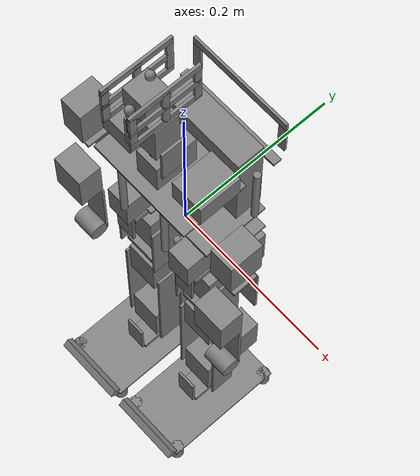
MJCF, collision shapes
<?xml version="1.0" ?>
<!-- Generated using onshape-to-robot -->
<!-- OnShape https://cad.onshape.com/documents/41654e89e61a392d020b728c/w/d555ceec170d351622b789de/e/4c9a04a707c36ac7ad2ca0f8 -->
<mujoco model="sigmaban2019_mujoco">
    <compiler angle="radian" meshdir="assets" autolimits="true"/>
    <option noslip_iterations="1"/>
    <default>
        <default class="sigmaban2019_mujoco">
            <joint frictionloss="0.1" armature="0.005"/>
            <position kp="50" dampratio="1"/>
            <default class="visual">
                <geom type="mesh" contype="0" conaffinity="0" group="2"/>
            </default>
            <default class="collision">
                <geom group="3"/>
            </default>
        </default>
    </default>
    <worldbody>
        <!-- Link tronc -->
        <body name="tronc" pos="0 0 0" quat="1 0 0 0" childclass="sigmaban2019_mujoco">
            <freejoint name="tronc_freejoint"/>
            <inertial pos="0.000280866 0.00434829 0.0901186" mass="1.49258" fullinertia="0.00652487 0.00716127 0.00434153 5.5354e-06 1.87301e-05 -0.000110706"/>
            <!-- Part handle -->
            <geom class="collision" pos="7.29591e-15 0.071323 0.1899" quat="0.5 0.5 0.5 -0.5" type="box" size="0.005 0.065 0.0015"/>
            <geom class="collision" pos="-0.06 0.071323 0.1649" quat="0.5 0.5 0.5 -0.5" type="box" size="0.02 0.005 0.0015"/>
            <geom class="collision" pos="0.06 0.071323 0.1649" quat="0.5 0.5 0.5 -0.5" type="box" size="0.02 0.005 0.0015"/>
            <!-- Mesh handle -->
            <geom type="mesh" class="visual" pos="7.16227e-15 0.072823 0.1449" quat="0.5 0.5 0.5 -0.5" mesh="handle" material="handle_material"/>
            <!-- Part mx64 -->
            <geom class="collision" pos="0.05 -0.017127 0.1609" quat="1.30215e-13 0.707107 1.91291e-13 0.707107" type="box" size="0.0145 0.025 0.02"/>
            <!-- Mesh mx64 -->
            <geom type="mesh" class="visual" pos="0.05 -0.032127 0.1609" quat="1.30215e-13 0.707107 1.91291e-13 0.707107" mesh="mx64" material="mx64_material"/>
            <!-- Part fr05_s101 -->
            <!-- Mesh fr05_s101 -->
            <geom type="mesh" class="visual" pos="-0.031 -0.046627 0.1369" quat="0.707107 0 1.11022e-16 0.707107" mesh="fr05_s101" material="fr05_s101_material"/>
            <!-- Part high_leg_protection_left -->
            <!-- Mesh high_leg_protection_left -->
            <geom type="mesh" class="visual" pos="-0.121675 -0.054354 -0.00350004" quat="1 0 0 4.00795e-13" mesh="high_leg_protection_left" material="high_leg_protection_left_material"/>
            <!-- Part mx64_2 -->
            <geom class="collision" pos="0.046375 -0.026254 0.02" quat="7.43046e-24 -4.30272e-14 1 8.97017e-25" type="box" size="0.0145 0.025 0.02"/>
            <!-- Mesh mx64_2 -->
            <geom type="mesh" class="visual" pos="0.046375 -0.011254 0.02" quat="7.43046e-24 -4.30272e-14 1 8.97017e-25" mesh="mx64" material="mx64_material"/>
            <!-- Part high_leg_protection_right -->
            <!-- Mesh high_leg_protection_right -->
            <geom type="mesh" class="visual" pos="0.031275 -0.054354 -0.00349999" quat="1 0 0 -1.70704e-13" mesh="high_leg_protection_right" material="high_leg_protection_right_material"/>
            <!-- Part mx64_3 -->
            <geom class="collision" pos="2.55418e-14 -0.022127 0.1623" quat="4.22162e-14 -5.63603e-16 -2.85882e-15 -1" type="box" size="0.0145 0.025 0.02"/>
            <!-- Mesh mx64_3 -->
            <geom type="mesh" class="visual" pos="2.67834e-14 -0.037127 0.1623" quat="4.22162e-14 -5.63603e-16 -2.85882e-15 -1" mesh="mx64" material="mx64_material"/>
            <!-- Part torso_top_plate_nuc -->
            <geom class="collision" pos="1.52206e-14 -0.019127 0.1354" quat="7.43046e-24 -4.31287e-14 1 8.97017e-25" type="box" size="0.065 0.04 0.0015"/>
            <!-- Mesh torso_top_plate_nuc -->
            <geom type="mesh" class="visual" pos="1.41856e-14 -0.007127 0.1369" quat="7.43046e-24 -4.31287e-14 1 8.97017e-25" mesh="torso_top_plate_nuc" material="torso_top_plate_nuc_material"/>
            <!-- Part pillar_tube -->
            <geom class="collision" pos="0.0625 0.037873 0.0909" quat="9.00389e-25 -1 -4.31664e-14 -7.43046e-24" type="cylinder" size="0.004 0.043"/>
            <!-- Mesh pillar_tube -->
            <geom type="mesh" class="visual" pos="0.0625 0.037873 0.1339" quat="9.00389e-25 -1 -4.31664e-14 -7.43046e-24" mesh="pillar_tube" material="pillar_tube_material"/>
            <!-- Part lipo_4s_2800mah -->
            <!-- Mesh lipo_4s_2800mah -->
            <geom type="mesh" class="visual" pos="-0.001 0.026123 0.0406" quat="9.35386e-19 1 4.31106e-14 2.68789e-17" mesh="lipo_4s_2800mah" material="lipo_4s_2800mah_material"/>
            <!-- Part fr08_b101 -->
            <!-- Mesh fr08_b101 -->
            <geom type="mesh" class="visual" pos="0.046375 -0.011254 0.02" quat="7.43165e-24 -4.31669e-14 1 8.96977e-25" mesh="fr08_b101" material="fr08_b101_material"/>
            <!-- Part pillar_tube_2 -->
            <geom class="collision" pos="-0.0625 0.037873 0.0909" quat="1 0 0 4.31664e-14" type="cylinder" size="0.004 0.043"/>
            <!-- Mesh pillar_tube_2 -->
            <geom type="mesh" class="visual" pos="-0.0625 0.037873 0.0479" quat="1 0 0 4.31664e-14" mesh="pillar_tube" material="pillar_tube_material"/>
            <!-- Part pillar_tube_3 -->
            <geom class="collision" pos="-0.031 -0.054127 0.0909" quat="1 0 -2.22045e-16 4.31664e-14" type="cylinder" size="0.004 0.043"/>
            <!-- Mesh pillar_tube_3 -->
            <geom type="mesh" class="visual" pos="-0.031 -0.054127 0.0479" quat="1 0 -2.22045e-16 4.31664e-14" mesh="pillar_tube" material="pillar_tube_material"/>
            <!-- Part mounting_block -->
            <!-- Mesh mounting_block -->
            <geom type="mesh" class="visual" pos="-0.0625 0.069823 0.1489" quat="3.05079e-14 -3.05081e-14 0.707107 -0.707107" mesh="mounting_block" material="mounting_block_material"/>
            <!-- Part torso_middle_plate_nuc -->
            <geom class="collision" pos="1.27053e-14 0.010373 0.0469" quat="1 -0 3.33067e-16 4.31664e-14" type="box" size="0.065 0.04 0.0015"/>
            <!-- Mesh torso_middle_plate_nuc -->
            <geom type="mesh" class="visual" pos="1.40003e-14 -0.004627 0.0454" quat="1 -0 3.33067e-16 4.31664e-14" mesh="torso_middle_plate_nuc" material="torso_middle_plate_nuc_material"/>
            <!-- Part piano_wire_back_fixation -->
            <!-- Mesh piano_wire_back_fixation -->
            <geom type="mesh" class="visual" pos="-0.052 0.066273 0.1459" quat="5.88841e-24 -0.707107 0.707107 -4.61984e-24" mesh="piano_wire_back_fixation" material="piano_wire_back_fixation_material"/>
            <!-- Part torso_bottom_plate_nuc -->
            <geom class="collision" pos="2.07506e-14 0.031123 0.00149996" quat="1 0 -2.08167e-17 4.30217e-14" type="box" size="0.065 0.022 0.0015"/>
            <geom class="collision" pos="-0.03 -0.007877 0.00149996" quat="1 0 -2.08167e-17 4.30217e-14" type="box" size="0.005 0.0175 0.0015"/>
            <geom class="collision" pos="0.03 -0.007877 0.00149996" quat="1 0 -2.08167e-17 4.30217e-14" type="box" size="0.005 0.0175 0.0015"/>
            <!-- Mesh torso_bottom_plate_nuc -->
            <geom type="mesh" class="visual" pos="2.27318e-14 0.008123 -4.21897e-08" quat="1 0 -2.08167e-17 4.30217e-14" mesh="torso_bottom_plate_nuc" material="torso_bottom_plate_nuc_material"/>
            <!-- Part fr08_b101_2 -->
            <!-- Mesh fr08_b101_2 -->
            <geom type="mesh" class="visual" pos="1.67532e-14 -0.037127 0.1623" quat="4.31643e-14 -0 -0 -1" mesh="fr08_b101" material="fr08_b101_material"/>
            <!-- Part dxlboard -->
            <!-- Mesh dxlboard -->
            <geom type="mesh" class="visual" pos="1.48671e-14 -0.015627 0.1274" quat="4.30993e-14 -0 1.11022e-16 -1" mesh="dxlboard" material="dxlboard_material"/>
            <!-- Part piano_wire_back_fixation_2 -->
            <!-- Mesh piano_wire_back_fixation_2 -->
            <geom type="mesh" class="visual" pos="0.06695 0.051323 0.1459" quat="2.33119e-17 3.13531e-13 -1 -7.86266e-19" mesh="piano_wire_back_fixation" material="piano_wire_back_fixation_material"/>
            <!-- Part fr05_s101_2 -->
            <!-- Mesh fr05_s101_2 -->
            <geom type="mesh" class="visual" pos="0.069 -0.046627 0.1369" quat="0.707107 -0 -1.11022e-16 0.707107" mesh="fr05_s101" material="fr05_s101_material"/>
            <!-- Part hotswap -->
            <!-- Mesh hotswap -->
            <geom type="mesh" class="visual" pos="-0.005 -0.011254 0.0534" quat="1 0 1.11022e-16 4.34047e-14" mesh="hotswap" material="hotswap_material"/>
            <!-- Part mx64_4 -->
            <geom class="collision" pos="-0.046375 -0.026254 0.02" quat="2.7363e-17 2.70308e-13 -1 -1.19699e-19" type="box" size="0.0145 0.025 0.02"/>
            <!-- Mesh mx64_4 -->
            <geom type="mesh" class="visual" pos="-0.046375 -0.011254 0.02" quat="2.7363e-17 2.70308e-13 -1 -1.19699e-19" mesh="mx64" material="mx64_material"/>
            <!-- Part nuc -->
            <geom class="collision" pos="1.24036e-14 0.035873 0.10615" quat="3.05866e-14 3.0454e-14 -0.707107 -0.707107" type="box" size="0.055 0.055 0.0165"/>
            <!-- Mesh nuc -->
            <geom type="mesh" class="visual" pos="1.37852e-14 0.019873 0.10615" quat="3.05866e-14 3.0454e-14 -0.707107 -0.707107" mesh="nuc" material="nuc_material"/>
            <!-- Part nuc_fix -->
            <geom class="collision" pos="8.35455e-15 0.059373 0.1384" quat="5.88841e-24 -0.707107 0.707107 -4.61984e-24" type="box" size="0.005 0.0675 0.0015"/>
            <!-- Mesh nuc_fix -->
            <geom type="mesh" class="visual" pos="8.95807e-15 0.052373 0.1399" quat="5.88841e-24 -0.707107 0.707107 -4.61984e-24" mesh="nuc_fix" material="nuc_fix_material"/>
            <!-- Part mounting_block_2 -->
            <!-- Mesh mounting_block_2 -->
            <geom type="mesh" class="visual" pos="0.0625 0.069823 0.1489" quat="3.05086e-14 -3.05103e-14 0.707107 -0.707107" mesh="mounting_block" material="mounting_block_material"/>
            <!-- Part fr08_b101_3 -->
            <!-- Mesh fr08_b101_3 -->
            <geom type="mesh" class="visual" pos="-0.046375 -0.011254 0.02" quat="7.43046e-24 -4.31044e-14 1 8.97017e-25" mesh="fr08_b101" material="fr08_b101_material"/>
            <!-- Part pillar_tube_4 -->
            <geom class="collision" pos="0.031 -0.054127 0.0914" quat="1 0 0 4.31664e-14" type="cylinder" size="0.004 0.043"/>
            <!-- Mesh pillar_tube_4 -->
            <geom type="mesh" class="visual" pos="0.031 -0.054127 0.0484" quat="1 0 0 4.31664e-14" mesh="pillar_tube" material="pillar_tube_material"/>
            <!-- Part mx64_5 -->
            <geom class="collision" pos="-0.0505868 -0.017127 0.1609" quat="3.00971e-14 0.707107 3.03091e-14 -0.707107" type="box" size="0.0145 0.025 0.02"/>
            <!-- Mesh mx64_5 -->
            <geom type="mesh" class="visual" pos="-0.0505868 -0.032127 0.1609" quat="3.00971e-14 0.707107 3.03091e-14 -0.707107" mesh="mx64" material="mx64_material"/>
            <!-- Part torsomarker -->
            <!-- Mesh torsomarker -->
            <geom type="mesh" class="visual" pos="1.82056e-14 -0.064127 0.0439" quat="1 0 0 4.30002e-14" mesh="torsomarker" material="torsomarker_material"/>
            <!-- Part torsoprotect -->
            <!-- Mesh torsoprotect -->
            <geom type="mesh" class="visual" pos="1.82056e-14 -0.064127 0.0439" quat="1 0 0 4.30002e-14" mesh="torsoprotect" material="torsoprotect_material"/>
            <!-- Part emergencymarker -->
            <!-- Mesh emergencymarker -->
            <geom type="mesh" class="visual" pos="1.82056e-14 -0.064127 0.0439" quat="1 0 0 4.30002e-14" mesh="emergencymarker" material="emergencymarker_material"/>
            <!-- Part backmarker -->
            <!-- Mesh backmarker -->
            <geom type="mesh" class="visual" pos="0.0005 0.057873 -4.21897e-08" quat="4.31952e-14 0 -1.11022e-16 -1" mesh="backmarker" material="backmarker_material"/>
            <!-- Part belt -->
            <!-- Mesh belt -->
            <geom type="mesh" class="visual" pos="0.0005 0.057873 -4.21897e-08" quat="4.31952e-14 0 -1.11022e-16 -1" mesh="belt" material="belt_material"/>
            <!-- Frame trunk (dummy link + fixed joint) -->
            <site name="trunk" pos="2.43796e-14 -0.011254 -0.0435" quat="0.707107 0 4.16334e-17 -0.707107"/>
            <!-- Frame head_base (dummy link + fixed joint) -->
            <site name="head_base" pos="2.67832e-14 -0.037127 0.1858" quat="0.707107 0 -1.11022e-16 -0.707107"/>
            <!-- Link u_block -->
            <body name="u_block" pos="-0.046375 -0.011254 -0.00350004" quat="0.707107 -0 -3.1225e-17 0.707107">
                <!-- Joint from tronc to u_block -->
                <joint name="right_hip_yaw" type="hinge"/>
                <inertial pos="-0.00607049 -2.12569e-09 -0.0117654" mass="0.0354404" fullinertia="8.64707e-06 2.30163e-05 2.00312e-05 -2.51587e-12 -7.76843e-07 -7.59825e-13"/>
                <!-- Part u_base_motors_blocs -->
                <geom class="collision" pos="-0.00494 0 -0.003" quat="0 1 0 0" type="box" size="0.025 0.015 0.003"/>
                <!-- Mesh u_base_motors_blocs -->
                <geom type="mesh" class="visual" pos="-0.03094 0.015 -4.33681e-19" quat="0 1 0 0" mesh="u_base_motors_blocs" material="u_base_motors_blocs_material"/>
                <!-- Part u_side_small -->
                <geom class="collision" pos="-0.03144 -3.46945e-17 -0.023" quat="0.5 -0.5 0.5 -0.5" type="box" size="0.0125 0.022 0.0015"/>
                <!-- Mesh u_side_small -->
                <geom type="mesh" class="visual" pos="-0.03294 0.015 8.67362e-18" quat="0.5 -0.5 0.5 -0.5" mesh="u_side_small" material="u_side_small_material"/>
                <!-- Part u_side_small_with_trace -->
                <geom class="collision" pos="0.0219 4.33681e-17 -0.023" quat="0.5 -0.5 -0.5 0.5" type="box" size="0.0135 0.021 0.0015"/>
                <!-- Mesh u_side_small_with_trace -->
                <geom type="mesh" class="visual" pos="0.0234 -0.015 6.50521e-18" quat="0.5 -0.5 -0.5 0.5" mesh="u_side_small_with_trace" material="u_side_small_with_trace_material"/>
                <!-- Link mx106_block_mir -->
                <body name="mx106_block_mir" pos="0.0234 3.46945e-17 -0.04" quat="0.5 0.5 -0.5 -0.5">
                    <!-- Joint from u_block to mx106_block_mir -->
                    <joint name="right_hip_roll" type="hinge"/>
                    <inertial pos="0.000708644 -0.0149916 0.004996" mass="0.293468" fullinertia="0.000351924 0.000307324 0.000137869 -3.56118e-06 -3.81447e-06 -2.48449e-05"/>
                    <!-- Part hn05_i101 -->
                    <!-- Mesh hn05_i101 -->
                    <geom type="mesh" class="visual" pos="-1.15741e-14 -1.66742e-14 0.04962" quat="0.184826 -4.20115e-14 -2.23377e-13 -0.982771" mesh="hn05_i101" material="hn05_i101_material"/>
                    <!-- Part mf128zz -->
                    <!-- Mesh mf128zz -->
                    <geom type="mesh" class="visual" pos="-1.15741e-14 -1.50782e-14 0.05318" quat="2.17694e-13 0.958428 0.285334 -6.48098e-14" mesh="mf128zz" material="mf128zz_material"/>
                    <!-- Part fr05_s101_3 -->
                    <!-- Mesh fr05_s101_3 -->
                    <geom type="mesh" class="visual" pos="0.019 0.0145 0.0474" quat="1.6061e-13 0.707107 -0.707107 1.6061e-13" mesh="fr05_s101" material="fr05_s101_material"/>
                    <!-- Part fr05_s101_4 -->
                    <!-- Mesh fr05_s101_4 -->
                    <geom type="mesh" class="visual" pos="0.019 -0.0505 -0.0006" quat="0.707107 -1.30104e-18 -5.71217e-19 0.707107" mesh="fr05_s101" material="fr05_s101_material"/>
                    <!-- Part fr08_b101_4 -->
                    <!-- Mesh fr08_b101_4 -->
                    <geom type="mesh" class="visual" pos="-1.15186e-15 -0.036 -0.026" quat="7.31951e-32 1 1.4444e-13 -9.53171e-30" mesh="fr08_b101" material="fr08_b101_material"/>
                    <!-- Part fr05_f101 -->
                    <!-- Mesh fr05_f101 -->
                    <geom type="mesh" class="visual" pos="-1.15741e-14 -1.77081e-14 0.0474" quat="1 -2.2688e-13 -1.11022e-16 1.45379e-13" mesh="fr05_f101" material="fr05_f101_material"/>
                    <!-- Part hn05_i101_2 -->
                    <!-- Mesh hn05_i101_2 -->
                    <geom type="mesh" class="visual" pos="0.02222 3.54577e-15 0.0234" quat="0.58776 -0.393113 0.58776 -0.393113" mesh="hn05_i101" material="hn05_i101_material"/>
                    <!-- Part mf128zz_2 -->
                    <!-- Mesh mf128zz_2 -->
                    <geom type="mesh" class="visual" pos="0.02578 4.57273e-15 0.0234" quat="0.693582 0.137637 -0.693582 -0.137637" mesh="mf128zz" material="mf128zz_material"/>
                    <!-- Part rx64_cap -->
                    <!-- Mesh rx64_cap -->
                    <geom type="mesh" class="visual" pos="0.0245 4.20497e-15 0.0234" quat="0.58776 -0.393113 0.58776 -0.393113" mesh="rx64_cap" material="rx64_cap_material"/>
                    <!-- Part mx106 -->
                    <geom class="collision" pos="-1.72422e-14 -0.015 0.0234" quat="0.707107 2.63118e-13 -0.707107 -5.83844e-14" type="box" size="0.015 0.0275 0.02"/>
                    <!-- Mesh mx106 -->
                    <geom type="mesh" class="visual" pos="-2.15869e-14 -2.88658e-15 0.0234" quat="0.707107 2.63118e-13 -0.707107 -5.83844e-14" mesh="mx106" material="mx106_material"/>
                    <!-- Part hn05_i101_3 -->
                    <!-- Mesh hn05_i101_3 -->
                    <geom type="mesh" class="visual" pos="0 0 -0.04822" quat="5.861e-29 0.285334 -0.958428 5.22146e-29" mesh="hn05_i101" material="hn05_i101_material"/>
                    <!-- Part mf128zz_3 -->
                    <!-- Mesh mf128zz_3 -->
                    <geom type="mesh" class="visual" pos="0 0 -0.05178" quat="0.879473 0 1.26218e-29 -0.47595" mesh="mf128zz" material="mf128zz_material"/>
                    <!-- Part rx64_cap_2 -->
                    <!-- Mesh rx64_cap_2 -->
                    <geom type="mesh" class="visual" pos="6.93889e-18 0 -0.0505" quat="5.861e-29 0.285334 -0.958428 5.22146e-29" mesh="rx64_cap" material="rx64_cap_material"/>
                    <!-- Part mx106_2 -->
                    <geom class="collision" pos="2.74835e-31 -0.015 -0.026" quat="1 -0 4.70321e-16 -2.51664e-16" type="box" size="0.015 0.0275 0.02"/>
                    <!-- Mesh mx106_2 -->
                    <geom type="mesh" class="visual" pos="0 0 -0.026" quat="1 -0 4.70321e-16 -2.51664e-16" mesh="mx106" material="mx106_material"/>
                    <!-- Link right_knee -->
                    <body name="right_knee" pos="-0.026 -1.04222e-14 0.0234" quat="0.707107 -1.02382e-13 0.707107 1.02293e-13">
                        <!-- Joint from mx106_block_mir to right_knee -->
                        <joint name="right_hip_pitch" type="hinge"/>
                        <inertial pos="0.000188839 -0.092394 0.0273957" mass="0.202752" fullinertia="0.000442788 9.69639e-05 0.000385387 -7.67062e-08 -2.55348e-08 1.17863e-05"/>
                        <!-- Part fr05_s101_5 -->
                        <!-- Mesh fr05_s101_5 -->
                        <geom type="mesh" class="visual" pos="-0.0145 -0.0855 0.007" quat="0.707107 0.707107 3.33067e-16 1.37705e-16" mesh="fr05_s101" material="fr05_s101_material"/>
                        <!-- Part hn05_i101_4 -->
                        <!-- Mesh hn05_i101_4 -->
                        <geom type="mesh" class="visual" pos="3.21514e-14 -0.14 0.04822" quat="0.988947 3.3207e-16 5.55112e-17 0.148266" mesh="hn05_i101" material="hn05_i101_material"/>
                        <!-- Part mf128zz_4 -->
                        <!-- Mesh mf128zz_4 -->
                        <geom type="mesh" class="visual" pos="3.21531e-14 -0.14 0.05178" quat="2.82326e-16 -0.831219 0.555945 1.6992e-16" mesh="mf128zz" material="mf128zz_material"/>
                        <!-- Part rx64_cap_3 -->
                        <!-- Mesh rx64_cap_3 -->
                        <geom type="mesh" class="visual" pos="3.21531e-14 -0.14 0.0505" quat="0.839328 2.25785e-16 0 -0.543625" mesh="rx64_cap" material="rx64_cap_material"/>
                        <!-- Part mx106_3 -->
                        <geom class="collision" pos="2.53143e-14 -0.125 0.026" quat="3.45758e-17 1 2.27443e-13 4.18167e-17" type="box" size="0.015 0.0275 0.02"/>
                        <!-- Mesh mx106_3 -->
                        <geom type="mesh" class="visual" pos="3.21514e-14 -0.14 0.026" quat="3.45758e-17 1 2.27443e-13 4.18167e-17" mesh="mx106" material="mx106_material"/>
                        <!-- Part u_base_64 -->
                        <geom class="collision" pos="3.71606e-16 -0.0825 0.026" quat="0.5 -0.5 0.5 0.5" type="box" size="0.0235 0.01375 0.003"/>
                        <!-- Mesh u_base_64 -->
                        <geom type="mesh" class="visual" pos="3.76435e-16 -0.0855 0.026" quat="0.5 -0.5 0.5 0.5" mesh="u_base_64" material="u_base_64_material"/>
                        <!-- Part u_side_femur_mir -->
                        <geom class="collision" pos="1.04229e-16 -0.0395 0.0535" quat="1 1.36709e-16 -1.11022e-16 1.33227e-15" type="box" size="0.02 0.045 0.0015"/>
                        <!-- Mesh u_side_femur_mir -->
                        <geom type="mesh" class="visual" pos="2.5327e-16 -0.0855 0.009" quat="1 1.36709e-16 -1.11022e-16 1.33227e-15" mesh="u_side_femur_mir" material="u_side_femur_mir_material"/>
                        <!-- Part u_side_femur -->
                        <geom class="collision" pos="4.15808e-32 -0.0395 -0.0015" quat="1 -0 -3.40873e-16 -7.80626e-17" type="box" size="0.02 0.045 0.0015"/>
                        <!-- Mesh u_side_femur -->
                        <geom type="mesh" class="visual" pos="0 -0.0855 -0.003" quat="1 -0 -3.40873e-16 -7.80626e-17" mesh="u_side_femur" material="u_side_femur_material"/>
                        <!-- Link tibia -->
                        <body name="tibia" pos="3.21514e-14 -0.14 3.60822e-16" quat="2.27318e-13 -1.79606e-16 4.996e-16 -1">
                            <!-- Joint from right_knee to tibia -->
                            <joint name="right_knee" type="hinge"/>
                            <inertial pos="-0.00342169 0.0646068 0.026" mass="0.0888437" fullinertia="0.000245247 7.67255e-05 0.000187463 -6.12719e-06 1.44286e-11 3.8066e-11"/>
                            <!-- Part tibia_plate -->
                            <geom class="collision" pos="-1.50984e-32 0.067 -0.0015" quat="0 1 0 0" type="box" size="0.015 0.0825 0.0015"/>
                            <!-- Mesh tibia_plate -->
                            <geom type="mesh" class="visual" pos="0 0 0" quat="0 1 0 0" mesh="tibia_plate" material="tibia_plate_material"/>
                            <!-- Part tibia_plate_2 -->
                            <geom class="collision" pos="5.06057e-18 0.067 0.0535" quat="9.4081e-16 -1 4.16334e-17 -1.47226e-16" type="box" size="0.015 0.0825 0.0015"/>
                            <!-- Mesh tibia_plate_2 -->
                            <geom type="mesh" class="visual" pos="-1.38778e-17 -1.11022e-16 0.055" quat="9.4081e-16 -1 4.16334e-17 -1.47226e-16" mesh="tibia_plate" material="tibia_plate_material"/>
                            <!-- Link mx106_block -->
                            <body name="mx106_block" pos="1.38778e-17 0.14 0" quat="6.93889e-17 -1.23334e-16 -7.77156e-16 1">
                                <!-- Joint from tibia to mx106_block -->
                                <joint name="right_ankle_pitch" type="hinge"/>
                                <inertial pos="0.0184063 0.0149916 0.027049" mass="0.293468" fullinertia="0.000137693 0.000307124 0.0003519 -2.48419e-05 5.67913e-06 3.25323e-06"/>
                                <!-- Part hn05_i101_5 -->
                                <!-- Mesh hn05_i101_5 -->
                                <geom type="mesh" class="visual" pos="-0.02622 9.76996e-15 0.026" quat="0.0238949 -0.706703 -0.0238949 0.706703" mesh="hn05_i101" material="hn05_i101_material"/>
                                <!-- Part mf128zz_5 -->
                                <!-- Mesh mf128zz_5 -->
                                <geom type="mesh" class="visual" pos="-0.02978 9.82547e-15 0.026" quat="0.697973 -0.113286 0.697973 -0.113286" mesh="mf128zz" material="mf128zz_material"/>
                                <!-- Part fr05_s101_6 -->
                                <!-- Mesh fr05_s101_6 -->
                                <geom type="mesh" class="visual" pos="-0.024 -0.0145 0.007" quat="0.5 0.5 0.5 0.5" mesh="fr05_s101" material="fr05_s101_material"/>
                                <!-- Part fr05_s101_7 -->
                                <!-- Mesh fr05_s101_7 -->
                                <geom type="mesh" class="visual" pos="0.024 0.0505 0.007" quat="0.5 0.5 -0.5 -0.5" mesh="fr05_s101" material="fr05_s101_material"/>
                                <!-- Part fr08_b101_5 -->
                                <!-- Mesh fr08_b101_5 -->
                                <geom type="mesh" class="visual" pos="0.0494 0.036 0.026" quat="0.707107 -7.64539e-17 0.707107 -2.22045e-16" mesh="fr08_b101" material="fr08_b101_material"/>
                                <!-- Part fr05_f101_2 -->
                                <!-- Mesh fr05_f101_2 -->
                                <geom type="mesh" class="visual" pos="-0.024 9.82547e-15 0.026" quat="1.18107e-16 -0.707107 2.22045e-16 0.707107" mesh="fr05_f101" material="fr05_f101_material"/>
                                <!-- Part hn05_i101_6 -->
                                <!-- Mesh hn05_i101_6 -->
                                <geom type="mesh" class="visual" pos="1.73472e-18 5.55112e-17 0.04822" quat="0.555945 4.01971e-16 -5.55112e-17 0.831219" mesh="hn05_i101" material="hn05_i101_material"/>
                                <!-- Part mf128zz_6 -->
                                <!-- Mesh mf128zz_6 -->
                                <geom type="mesh" class="visual" pos="3.46945e-18 5.55112e-17 0.05178" quat="2.13121e-16 0.194648 -0.980873 -3.52648e-16" mesh="mf128zz" material="mf128zz_material"/>
                                <!-- Part rx64_cap_4 -->
                                <!-- Mesh rx64_cap_4 -->
                                <geom type="mesh" class="visual" pos="0 5.55112e-17 0.0505" quat="8.21843e-14 2.97359e-16 -1.11022e-16 1" mesh="rx64_cap" material="rx64_cap_material"/>
                                <!-- Part mx106_4 -->
                                <geom class="collision" pos="1.63291e-31 0.015 0.026" quat="0 1 0 0" type="box" size="0.015 0.0275 0.02"/>
                                <!-- Mesh mx106_4 -->
                                <geom type="mesh" class="visual" pos="0 0 0.026" quat="0 1 0 0" mesh="mx106" material="mx106_material"/>
                                <!-- Part hn05_i101_7 -->
                                <!-- Mesh hn05_i101_7 -->
                                <geom type="mesh" class="visual" pos="0.07162 4.44089e-15 0.026" quat="0.697973 -0.113286 0.697973 -0.113286" mesh="hn05_i101" material="hn05_i101_material"/>
                                <!-- Part mf128zz_7 -->
                                <!-- Mesh mf128zz_7 -->
                                <geom type="mesh" class="visual" pos="0.07518 4.44089e-15 0.026" quat="0.413436 -0.573647 -0.413436 0.573647" mesh="mf128zz" material="mf128zz_material"/>
                                <!-- Part rx64_cap_5 -->
                                <!-- Mesh rx64_cap_5 -->
                                <geom type="mesh" class="visual" pos="0.0739 4.4964e-15 0.026" quat="0.697973 -0.113286 0.697973 -0.113286" mesh="rx64_cap" material="rx64_cap_material"/>
                                <!-- Part mx106_5 -->
                                <geom class="collision" pos="0.0494 0.015 0.026" quat="1.02674e-13 -0.707107 -1.02585e-13 0.707107" type="box" size="0.015 0.0275 0.02"/>
                                <!-- Mesh mx106_5 -->
                                <geom type="mesh" class="visual" pos="0.0494 4.4964e-15 0.026" quat="1.02674e-13 -0.707107 -1.02585e-13 0.707107" mesh="mx106" material="mx106_material"/>
                                <!-- Link right_foot_cleat_back_left -->
                                <body name="right_foot_cleat_back_left" pos="0.0234 4.55191e-15 0.026" quat="0.707107 -9.75986e-16 -0.707107 9.99201e-16">
                                    <!-- Joint from mx106_block to right_foot_cleat_back_left -->
                                    <joint name="right_ankle_roll" type="hinge"/>
                                    <inertial pos="-0.00468466 -0.0365779 0.0511529" mass="0.239067" fullinertia="0.000628183 0.000791509 0.000201629 -1.62629e-06 4.22638e-06 -2.53047e-05"/>
                                    <!-- Part gauge_protection_lateral -->
                                    <!-- Mesh gauge_protection_lateral -->
                                    <geom type="mesh" class="visual" pos="0.0425 -0.0431 0.11867" quat="9.99201e-16 9.49699e-16 0.707107 0.707107" mesh="gauge_protection_lateral" material="gauge_protection_lateral_material"/>
                                    <!-- Part mounting_block_3 -->
                                    <!-- Mesh mounting_block_3 -->
                                    <geom type="mesh" class="visual" pos="-0.0525 -0.037 0.00867" quat="1.03822e-15 0.707107 -8.88178e-16 0.707107" mesh="mounting_block" material="mounting_block_material"/>
                                    <!-- Part foot_protection -->
                                    <geom class="collision" pos="-0.0055 -0.0275 0.12247" quat="0.270598 -0.653281 0.653281 0.270598" type="box" size="0.005 0.045 0.005"/>
                                    <!-- Mesh foot_protection -->
                                    <geom type="mesh" class="visual" pos="-0.033 -0.04 0.10347" quat="0.5 -0.5 0.5 0.5" mesh="foot_protection" material="foot_protection_material"/>
                                    <!-- Part mounting_block_4 -->
                                    <!-- Mesh mounting_block_4 -->
                                    <geom type="mesh" class="visual" pos="0.0415 -0.037 0.06867" quat="0.707107 -1.03822e-15 -0.707107 -8.88178e-16" mesh="mounting_block" material="mounting_block_material"/>
                                    <!-- Part foot_plate -->
                                    <geom class="collision" pos="-0.0055 -0.0415 0.03867" quat="1.05471e-15 8.82482e-16 0.707107 0.707107" type="box" size="0.045 0.0775 0.0015"/>
                                    <!-- Mesh foot_plate -->
                                    <geom type="mesh" class="visual" pos="-0.0055 -0.043 0.03867" quat="1.05471e-15 8.82482e-16 0.707107 0.707107" mesh="foot_plate" material="foot_plate_material"/>
                                    <!-- Part gauge_protection_lateral_2 -->
                                    <!-- Mesh gauge_protection_lateral_2 -->
                                    <geom type="mesh" class="visual" pos="-0.0535 -0.0431 -0.04133" quat="0.707107 -0.707107 9.99201e-16 -8.88249e-16" mesh="gauge_protection_lateral" material="gauge_protection_lateral_material"/>
                                    <!-- Part mounting_block_5 -->
                                    <!-- Mesh mounting_block_5 -->
                                    <geom type="mesh" class="visual" pos="-0.0525 -0.037 0.06867" quat="1.03441e-15 0.707107 -8.88178e-16 0.707107" mesh="mounting_block" material="mounting_block_material"/>
                                    <!-- Part mounting_block_6 -->
                                    <!-- Mesh mounting_block_6 -->
                                    <geom type="mesh" class="visual" pos="0.0415 -0.037 0.00867" quat="0.707107 -1.04521e-15 -0.707107 -9.99201e-16" mesh="mounting_block" material="mounting_block_material"/>
                                    <!-- Part u_base_motors_blocs_2 -->
                                    <geom class="collision" pos="1.73472e-17 -0.037 0.02834" quat="0.5 -0.5 0.5 0.5" type="box" size="0.025 0.015 0.003"/>
                                    <!-- Mesh u_base_motors_blocs_2 -->
                                    <geom type="mesh" class="visual" pos="0.015 -0.04 0.05434" quat="0.5 -0.5 0.5 0.5" mesh="u_base_motors_blocs" material="u_base_motors_blocs_material"/>
                                    <!-- Part u_side_small_2 -->
                                    <geom class="collision" pos="6.76542e-17 -0.017 0.05484" quat="1.38778e-16 1.40869e-15 1 -4.51028e-16" type="box" size="0.0125 0.022 0.0015"/>
                                    <!-- Mesh u_side_small_2 -->
                                    <geom type="mesh" class="visual" pos="0.015 -0.04 0.05634" quat="1.38778e-16 1.40869e-15 1 -4.51028e-16" mesh="u_side_small" material="u_side_small_material"/>
                                    <!-- Part u_side_small_with_trace_2 -->
                                    <geom class="collision" pos="6.93889e-18 -0.017 0.0015" quat="1 -0 -2.84495e-16 6.93889e-18" type="box" size="0.0135 0.021 0.0015"/>
                                    <!-- Mesh u_side_small_with_trace_2 -->
                                    <geom type="mesh" class="visual" pos="-0.015 -0.04 0" quat="1 -0 -2.84495e-16 6.93889e-18" mesh="u_side_small_with_trace" material="u_side_small_with_trace_material"/>
                                    <!-- Part load_cell_40kg -->
                                    <!-- Mesh load_cell_40kg -->
                                    <geom type="mesh" class="visual" pos="0.0325 -0.04 0.09597" quat="9.15934e-16 1.15071e-15 0.707107 0.707107" mesh="load_cell_40kg" material="load_cell_40kg_material"/>
                                    <!-- Part nylon_ring -->
                                    <!-- Mesh nylon_ring -->
                                    <geom type="mesh" class="visual" pos="0.0325 -0.044 0.10947" quat="0.0704968 -0.0704968 0.703584 0.703584" mesh="nylon_ring" material="nylon_ring_material"/>
                                    <!-- Part cleat -->
                                    <geom class="collision" pos="0.0325 -0.05 0.10947" quat="0.680034 0.680034 0.193789 -0.193789" type="cylinder" size="0.008 0.01"/>
                                    <!-- Mesh cleat -->
                                    <geom type="mesh" class="visual" pos="0.0325 -0.06 0.10947" quat="0.961713 8.45022e-17 0.274058 -1.22125e-15" mesh="cleat" material="cleat_material"/>
                                    <!-- Part load_cell_40kg_2 -->
                                    <!-- Mesh load_cell_40kg_2 -->
                                    <geom type="mesh" class="visual" pos="-0.0435 -0.04 0.09597" quat="9.99201e-16 7.13213e-16 0.707107 0.707107" mesh="load_cell_40kg" material="load_cell_40kg_material"/>
                                    <!-- Part nylon_ring_2 -->
                                    <!-- Mesh nylon_ring_2 -->
                                    <geom type="mesh" class="visual" pos="-0.0435 -0.044 0.10947" quat="0.0704968 -0.0704968 0.703584 0.703584" mesh="nylon_ring" material="nylon_ring_material"/>
                                    <!-- Part cleat_2 -->
                                    <geom class="collision" pos="-0.0435 -0.05 0.10947" quat="0.0704968 0.0704968 0.703584 -0.703584" type="cylinder" size="0.008 0.01"/>
                                    <!-- Mesh cleat_2 -->
                                    <geom type="mesh" class="visual" pos="-0.0435 -0.06 0.10947" quat="0.0996976 1.57175e-15 0.995018 -3.46945e-16" mesh="cleat" material="cleat_material"/>
                                    <!-- Part load_cell_40kg_3 -->
                                    <!-- Mesh load_cell_40kg_3 -->
                                    <geom type="mesh" class="visual" pos="0.0325 -0.04 -0.01863" quat="0.707107 -0.707107 5.55112e-16 -1.30583e-15" mesh="load_cell_40kg" material="load_cell_40kg_material"/>
                                    <!-- Part nylon_ring_3 -->
                                    <!-- Mesh nylon_ring_3 -->
                                    <geom type="mesh" class="visual" pos="0.0325 -0.044 -0.03213" quat="0.0704968 -0.0704968 0.703584 0.703584" mesh="nylon_ring" material="nylon_ring_material"/>
                                    <!-- Part cleat_3 -->
                                    <geom class="collision" pos="0.0325 -0.05 -0.03213" quat="0.69855 0.69855 -0.109672 0.109672" type="cylinder" size="0.008 0.01"/>
                                    <!-- Mesh cleat_3 -->
                                    <geom type="mesh" class="visual" pos="0.0325 -0.06 -0.03213" quat="0.987899 -7.30371e-16 -0.1551 -1.07553e-15" mesh="cleat" material="cleat_material"/>
                                    <!-- Part load_cell_40kg_4 -->
                                    <!-- Mesh load_cell_40kg_4 -->
                                    <geom type="mesh" class="visual" pos="-0.0435 -0.04 -0.01863" quat="0.707107 -0.707107 1.33227e-15 -6.95048e-16" mesh="load_cell_40kg" material="load_cell_40kg_material"/>
                                    <!-- Part nylon_ring_4 -->
                                    <!-- Mesh nylon_ring_4 -->
                                    <geom type="mesh" class="visual" pos="-0.0435 -0.044 -0.03213" quat="0.0704968 -0.0704968 0.703584 0.703584" mesh="nylon_ring" material="nylon_ring_material"/>
                                    <!-- Part cleat_4 -->
                                    <geom class="collision" pos="-0.0435 -0.05 -0.03213" quat="0.0704968 0.0704968 0.703584 -0.703584" type="cylinder" size="0.008 0.01"/>
                                    <!-- Mesh cleat_4 -->
                                    <geom type="mesh" class="visual" pos="-0.0435 -0.06 -0.03213" quat="0.0996976 1.60231e-15 0.995018 -4.92661e-16" mesh="cleat" material="cleat_material"/>
                                    <!-- Frame right_foot (dummy link + fixed joint) -->
                                    <site name="right_foot" pos="-5.55112e-17 -0.06 0.02317" quat="0.5 -0.5 -0.5 -0.5"/>
                                </body>
                            </body>
                        </body>
                    </body>
                </body>
            </body>
            <!-- Link u_block_2 -->
            <body name="u_block_2" pos="0.046375 -0.011254 -0.00349999" quat="0.707107 9.55185e-17 2.22045e-16 0.707107">
                <!-- Joint from tronc to u_block_2 -->
                <joint name="left_hip_yaw" type="hinge"/>
                <inertial pos="-0.00607049 -2.12569e-09 -0.0117654" mass="0.0354404" fullinertia="8.64707e-06 2.30163e-05 2.00312e-05 -2.51587e-12 -7.76843e-07 -7.59825e-13"/>
                <!-- Part u_base_motors_blocs_3 -->
                <geom class="collision" pos="-0.00494 6.93889e-18 -0.003" quat="0 1 0 0" type="box" size="0.025 0.015 0.003"/>
                <!-- Mesh u_base_motors_blocs_3 -->
                <geom type="mesh" class="visual" pos="-0.03094 0.015 0" quat="0 1 0 0" mesh="u_base_motors_blocs" material="u_base_motors_blocs_material"/>
                <!-- Part u_side_small_3 -->
                <geom class="collision" pos="-0.03144 6.93889e-18 -0.023" quat="0.5 -0.5 0.5 -0.5" type="box" size="0.0125 0.022 0.0015"/>
                <!-- Mesh u_side_small_3 -->
                <geom type="mesh" class="visual" pos="-0.03294 0.015 4.33681e-18" quat="0.5 -0.5 0.5 -0.5" mesh="u_side_small" material="u_side_small_material"/>
                <!-- Part u_side_small_with_trace_3 -->
                <geom class="collision" pos="0.0219 5.20417e-18 -0.023" quat="0.5 -0.5 -0.5 0.5" type="box" size="0.0135 0.021 0.0015"/>
                <!-- Mesh u_side_small_with_trace_3 -->
                <geom type="mesh" class="visual" pos="0.0234 -0.015 5.20417e-18" quat="0.5 -0.5 -0.5 0.5" mesh="u_side_small_with_trace" material="u_side_small_with_trace_material"/>
                <!-- Link mx106_block_2 -->
                <body name="mx106_block_2" pos="0.0234 6.93889e-18 -0.04" quat="0.5 0.5 -0.5 -0.5">
                    <!-- Joint from u_block_2 to mx106_block_2 -->
                    <joint name="left_hip_roll" type="hinge"/>
                    <inertial pos="-0.00104898 -0.0149916 0.00499375" mass="0.293468" fullinertia="0.0003519 0.000307124 0.000137693 3.25323e-06 5.67913e-06 -2.48419e-05"/>
                    <!-- Part hn05_i101_8 -->
                    <!-- Mesh hn05_i101_8 -->
                    <geom type="mesh" class="visual" pos="-1.16018e-14 -5.05151e-15 0.04962" quat="0.770508 -1.08226e-16 -2.77556e-16 -0.63743" mesh="hn05_i101" material="hn05_i101_material"/>
                    <!-- Part mf128zz_8 -->
                    <!-- Mesh mf128zz_8 -->
                    <geom type="mesh" class="visual" pos="-1.16018e-14 -5.05151e-15 0.05318" quat="1.8597e-16 0.476312 0.879276 -1.43125e-16" mesh="mf128zz" material="mf128zz_material"/>
                    <!-- Part fr05_s101_8 -->
                    <!-- Mesh fr05_s101_8 -->
                    <geom type="mesh" class="visual" pos="0.019 0.0145 0.0474" quat="1.92815e-17 0.707107 -0.707107 2.52996e-16" mesh="fr05_s101" material="fr05_s101_material"/>
                    <!-- Part fr05_s101_9 -->
                    <!-- Mesh fr05_s101_9 -->
                    <geom type="mesh" class="visual" pos="0.019 -0.0505 -0.0006" quat="0.707107 6.2717e-17 -5.55112e-17 0.707107" mesh="fr05_s101" material="fr05_s101_material"/>
                    <!-- Part fr08_b101_6 -->
                    <!-- Mesh fr08_b101_6 -->
                    <geom type="mesh" class="visual" pos="-1.16573e-15 -0.036 -0.026" quat="5.91621e-16 1 1.44348e-13 -8.22444e-17" mesh="fr08_b101" material="fr08_b101_material"/>
                    <!-- Part fr05_f101_3 -->
                    <!-- Mesh fr05_f101_3 -->
                    <geom type="mesh" class="visual" pos="-1.15949e-14 -5.05151e-15 0.0474" quat="1 -1.80342e-17 -1.11022e-16 1.44301e-13" mesh="fr05_f101" material="fr05_f101_material"/>
                    <!-- Part hn05_i101_9 -->
                    <!-- Mesh hn05_i101_9 -->
                    <geom type="mesh" class="visual" pos="-0.02222 -1.4086e-15 0.0234" quat="0.0516026 -0.705221 -0.0516026 0.705221" mesh="hn05_i101" material="hn05_i101_material"/>
                    <!-- Part mf128zz_9 -->
                    <!-- Mesh mf128zz_9 -->
                    <geom type="mesh" class="visual" pos="-0.02578 -2.43555e-15 0.0234" quat="0.535155 -0.462178 0.535155 -0.462178" mesh="mf128zz" material="mf128zz_material"/>
                    <!-- Part rx64_cap_6 -->
                    <!-- Mesh rx64_cap_6 -->
                    <geom type="mesh" class="visual" pos="-0.0245 -2.06779e-15 0.0234" quat="0.0462153 -0.705595 -0.0462153 0.705595" mesh="rx64_cap" material="rx64_cap_material"/>
                    <!-- Part mx106_6 -->
                    <geom class="collision" pos="-1.72918e-14 -0.015 0.0234" quat="0.707107 -1.01897e-13 0.707107 1.02005e-13" type="box" size="0.015 0.0275 0.02"/>
                    <!-- Mesh mx106_6 -->
                    <geom type="mesh" class="visual" pos="-2.16216e-14 4.98213e-15 0.0234" quat="0.707107 -1.01897e-13 0.707107 1.02005e-13" mesh="mx106" material="mx106_material"/>
                    <!-- Part hn05_i101_10 -->
                    <!-- Mesh hn05_i101_10 -->
                    <geom type="mesh" class="visual" pos="-6.93889e-18 0 -0.04822" quat="2.43136e-16 -0.879276 0.476312 2.50677e-17" mesh="hn05_i101" material="hn05_i101_material"/>
                    <!-- Part mf128zz_10 -->
                    <!-- Mesh mf128zz_10 -->
                    <geom type="mesh" class="visual" pos="-6.93889e-18 0 -0.05178" quat="0.284939 1.36941e-16 2.22045e-16 -0.958546" mesh="mf128zz" material="mf128zz_material"/>
                    <!-- Part rx64_cap_7 -->
                    <!-- Mesh rx64_cap_7 -->
                    <geom type="mesh" class="visual" pos="-6.93889e-18 0 -0.0505" quat="2.31952e-16 -0.879276 0.476312 3.8288e-17" mesh="rx64_cap" material="rx64_cap_material"/>
                    <!-- Part mx106_7 -->
                    <geom class="collision" pos="-6.93889e-18 -0.015 -0.026" quat="1 0 2.64545e-17 8.67362e-19" type="box" size="0.015 0.0275 0.02"/>
                    <!-- Mesh mx106_7 -->
                    <geom type="mesh" class="visual" pos="-6.93889e-18 0 -0.026" quat="1 0 2.64545e-17 8.67362e-19" mesh="mx106" material="mx106_material"/>
                    <!-- Link left_knee -->
                    <body name="left_knee" pos="0.026 1.24623e-14 0.0234" quat="1.02086e-13 -0.707107 -1.01585e-13 -0.707107">
                        <!-- Joint from mx106_block_2 to left_knee -->
                        <joint name="left_hip_pitch" type="hinge"/>
                        <inertial pos="-0.000185582 0.092394 -0.0271483" mass="0.202752" fullinertia="0.000442915 9.70917e-05 0.000385387 -1.01212e-07 1.22181e-07 1.18508e-05"/>
                        <!-- Part fr05_s101_10 -->
                        <!-- Mesh fr05_s101_10 -->
                        <geom type="mesh" class="visual" pos="0.0145 0.0855 -0.045" quat="4.44089e-16 1.14858e-16 0.707107 0.707107" mesh="fr05_s101" material="fr05_s101_material"/>
                        <!-- Part hn05_i101_11 -->
                        <!-- Mesh hn05_i101_11 -->
                        <geom type="mesh" class="visual" pos="-3.16379e-14 0.14 -0.04822" quat="2.8673e-16 -0.970625 -0.240598 -1.61135e-16" mesh="hn05_i101" material="hn05_i101_material"/>
                        <!-- Part mf128zz_11 -->
                        <!-- Mesh mf128zz_11 -->
                        <geom type="mesh" class="visual" pos="-3.16362e-14 0.14 -0.05178" quat="0.555945 1.03616e-16 -3.19189e-16 0.831219" mesh="mf128zz" material="mf128zz_material"/>
                        <!-- Part rx64_cap_8 -->
                        <!-- Mesh rx64_cap_8 -->
                        <geom type="mesh" class="visual" pos="-3.16362e-14 0.14 -0.0505" quat="9.29567e-17 -0.568145 -0.822929 -3.08846e-16" mesh="rx64_cap" material="rx64_cap_material"/>
                        <!-- Part mx106_8 -->
                        <geom class="collision" pos="-2.4828e-14 0.125 -0.026" quat="1 3.18902e-16 1.11022e-16 2.26902e-13" type="box" size="0.015 0.0275 0.02"/>
                        <!-- Mesh mx106_8 -->
                        <geom type="mesh" class="visual" pos="-3.16379e-14 0.14 -0.026" quat="1 3.18902e-16 1.11022e-16 2.26902e-13" mesh="mx106" material="mx106_material"/>
                        <!-- Part u_base_64_2 -->
                        <geom class="collision" pos="6.2117e-17 0.0825 -0.026" quat="0.5 0.5 -0.5 0.5" type="box" size="0.0235 0.01375 0.003"/>
                        <!-- Mesh u_base_64_2 -->
                        <geom type="mesh" class="visual" pos="6.245e-17 0.0855 -0.026" quat="0.5 0.5 -0.5 0.5" mesh="u_base_64" material="u_base_64_material"/>
                        <!-- Part u_side_femur_mir_2 -->
                        <geom class="collision" pos="4.36598e-17 0.0395 -0.0535" quat="1.39274e-16 -1 2.0195e-16 -1.80944e-17" type="box" size="0.02 0.045 0.0015"/>
                        <!-- Mesh u_side_femur_mir_2 -->
                        <geom type="mesh" class="visual" pos="5.55112e-17 0.0855 -0.009" quat="1.39274e-16 -1 2.0195e-16 -1.80944e-17" mesh="u_side_femur_mir" material="u_side_femur_mir_material"/>
                        <!-- Part u_side_femur_2 -->
                        <geom class="collision" pos="1.73472e-18 0.0395 0.0015" quat="0 1 0 0" type="box" size="0.02 0.045 0.0015"/>
                        <!-- Mesh u_side_femur_2 -->
                        <geom type="mesh" class="visual" pos="1.73472e-18 0.0855 0.003" quat="0 1 0 0" mesh="u_side_femur" material="u_side_femur_material"/>
                        <!-- Link tibia_2 -->
                        <body name="tibia_2" pos="-3.16396e-14 0.14 1.9984e-14" quat="1 5.59291e-16 -2.22045e-16 2.28274e-13">
                            <!-- Joint from left_knee to tibia_2 -->
                            <joint name="left_knee" type="hinge"/>
                            <inertial pos="-0.00342169 0.0646068 -0.026" mass="0.0888437" fullinertia="0.000245247 7.67255e-05 0.000187463 -6.12719e-06 1.44286e-11 3.8066e-11"/>
                            <!-- Part tibia_plate_3 -->
                            <geom class="collision" pos="2.23209e-16 0.067 -0.0535" quat="2.31075e-16 1 -7.56747e-16 3.23483e-17" type="box" size="0.015 0.0825 0.0015"/>
                            <!-- Mesh tibia_plate_3 -->
                            <geom type="mesh" class="visual" pos="0 0 -0.052" quat="2.31075e-16 1 -7.56747e-16 3.23483e-17" mesh="tibia_plate" material="tibia_plate_material"/>
                            <!-- Part tibia_plate_4 -->
                            <geom class="collision" pos="-5.58374e-31 0.067 0.0015" quat="0 1 0 0" type="box" size="0.015 0.0825 0.0015"/>
                            <!-- Mesh tibia_plate_4 -->
                            <geom type="mesh" class="visual" pos="0 0 0.003" quat="0 1 0 0" mesh="tibia_plate" material="tibia_plate_material"/>
                            <!-- Link mx106_block_mir_2 -->
                            <body name="mx106_block_mir_2" pos="1.56125e-17 0.14 0" quat="1 -2.60562e-16 -0 -1.20823e-15">
                                <!-- Joint from tibia_2 to mx106_block_mir_2 -->
                                <joint name="left_ankle_pitch" type="hinge"/>
                                <inertial pos="-0.018404 -0.0149916 -0.0267086" mass="0.293468" fullinertia="0.000137869 0.000307324 0.000351924 -2.48449e-05 3.81447e-06 3.56118e-06"/>
                                <!-- Part hn05_i101_12 -->
                                <!-- Mesh hn05_i101_12 -->
                                <geom type="mesh" class="visual" pos="0.02622 -5.9952e-15 -0.026" quat="0.387533 -0.591454 0.387533 -0.591454" mesh="hn05_i101" material="hn05_i101_material"/>
                                <!-- Part mf128zz_12 -->
                                <!-- Mesh mf128zz_12 -->
                                <geom type="mesh" class="visual" pos="0.02978 -4.38538e-15 -0.026" quat="0.707107 3.07503e-13 -0.707107 1.32307e-14" mesh="mf128zz" material="mf128zz_material"/>
                                <!-- Part fr05_s101_11 -->
                                <!-- Mesh fr05_s101_11 -->
                                <geom type="mesh" class="visual" pos="0.024 0.0145 -0.045" quat="0.5 0.5 -0.5 -0.5" mesh="fr05_s101" material="fr05_s101_material"/>
                                <!-- Part fr05_s101_12 -->
                                <!-- Mesh fr05_s101_12 -->
                                <geom type="mesh" class="visual" pos="-0.024 -0.0505 -0.045" quat="0.5 0.5 0.5 0.5" mesh="fr05_s101" material="fr05_s101_material"/>
                                <!-- Part fr08_b101_7 -->
                                <!-- Mesh fr08_b101_7 -->
                                <geom type="mesh" class="visual" pos="-0.0494 -0.036 -0.026" quat="1.61141e-13 0.707107 1.60427e-13 -0.707107" mesh="fr08_b101" material="fr08_b101_material"/>
                                <!-- Part fr05_f101_4 -->
                                <!-- Mesh fr05_f101_4 -->
                                <geom type="mesh" class="visual" pos="0.024 -6.93889e-15 -0.026" quat="0.707107 -1.60288e-13 0.707107 1.60177e-13" mesh="fr05_f101" material="fr05_f101_material"/>
                                <!-- Part hn05_i101_13 -->
                                <!-- Mesh hn05_i101_13 -->
                                <geom type="mesh" class="visual" pos="0 0 -0.04822" quat="8.03529e-17 -3.65557e-13 -1 -2.78098e-17" mesh="hn05_i101" material="hn05_i101_material"/>
                                <!-- Part mf128zz_13 -->
                                <!-- Mesh mf128zz_13 -->
                                <geom type="mesh" class="visual" pos="1.73472e-18 0 -0.05178" quat="0.707107 -0 -1.38778e-17 0.707107" mesh="mf128zz" material="mf128zz_material"/>
                                <!-- Part rx64_cap_9 -->
                                <!-- Mesh rx64_cap_9 -->
                                <geom type="mesh" class="visual" pos="1.73472e-18 0 -0.0505" quat="6.50521e-19 -3.65529e-13 -1 -2.77882e-17" mesh="rx64_cap" material="rx64_cap_material"/>
                                <!-- Part mx106_9 -->
                                <geom class="collision" pos="1.73472e-18 -0.015 -0.026" quat="1 0 -1.6778e-29 -1.6155e-27" type="box" size="0.015 0.0275 0.02"/>
                                <!-- Mesh mx106_9 -->
                                <geom type="mesh" class="visual" pos="1.73472e-18 0 -0.026" quat="1 0 -1.6778e-29 -1.6155e-27" mesh="mx106" material="mx106_material"/>
                                <!-- Part hn05_i101_14 -->
                                <!-- Mesh hn05_i101_14 -->
                                <geom type="mesh" class="visual" pos="-0.07162 -2.9643e-14 -0.026" quat="0.707107 1.58955e-13 -0.707107 1.62648e-13" mesh="hn05_i101" material="hn05_i101_material"/>
                                <!-- Part mf128zz_14 -->
                                <!-- Mesh mf128zz_14 -->
                                <geom type="mesh" class="visual" pos="-0.07518 -3.12528e-14 -0.026" quat="0.5 0.5 0.5 0.5" mesh="mf128zz" material="mf128zz_material"/>
                                <!-- Part rx64_cap_10 -->
                                <!-- Mesh rx64_cap_10 -->
                                <geom type="mesh" class="visual" pos="-0.0739 -3.06422e-14 -0.026" quat="0.707107 1.58982e-13 -0.707107 1.62676e-13" mesh="rx64_cap" material="rx64_cap_material"/>
                                <!-- Part mx106_10 -->
                                <geom class="collision" pos="-0.0494 -0.015 -0.026" quat="0.707107 -2.63318e-13 0.707107 5.83393e-14" type="box" size="0.015 0.0275 0.02"/>
                                <!-- Mesh mx106_10 -->
                                <geom type="mesh" class="visual" pos="-0.0494 -1.95399e-14 -0.026" quat="0.707107 -2.63318e-13 0.707107 5.83393e-14" mesh="mx106" material="mx106_material"/>
                                <!-- Link left_foot_cleat_front_right -->
                                <body name="left_foot_cleat_front_right" pos="-0.0234 -7.71605e-15 -0.026" quat="1.586e-13 -0.707107 -1.63092e-13 -0.707107">
                                    <!-- Joint from mx106_block_mir_2 to left_foot_cleat_front_right -->
                                    <joint name="left_ankle_roll" type="hinge"/>
                                    <inertial pos="0.00468466 -0.0365779 0.0511529" mass="0.239067" fullinertia="0.000628183 0.000791509 0.000201629 1.62629e-06 -4.22638e-06 -2.53047e-05"/>
                                    <!-- Part gauge_protection_lateral_3 -->
                                    <!-- Mesh gauge_protection_lateral_3 -->
                                    <geom type="mesh" class="visual" pos="0.0535 -0.0431 0.11867" quat="2.77556e-16 4.11863e-16 -0.707107 -0.707107" mesh="gauge_protection_lateral" material="gauge_protection_lateral_material"/>
                                    <!-- Part mounting_block_7 -->
                                    <!-- Mesh mounting_block_7 -->
                                    <geom type="mesh" class="visual" pos="-0.0415 -0.037 0.00867" quat="3.04743e-16 -0.707107 3.33067e-16 -0.707107" mesh="mounting_block" material="mounting_block_material"/>
                                    <!-- Part foot_protection_2 -->
                                    <geom class="collision" pos="0.0055 -0.0275 0.12247" quat="0.270598 -0.653281 0.653281 0.270598" type="box" size="0.005 0.045 0.005"/>
                                    <!-- Mesh foot_protection_2 -->
                                    <geom type="mesh" class="visual" pos="-0.022 -0.04 0.10347" quat="0.5 -0.5 0.5 0.5" mesh="foot_protection" material="foot_protection_material"/>
                                    <!-- Part mounting_block_8 -->
                                    <!-- Mesh mounting_block_8 -->
                                    <geom type="mesh" class="visual" pos="0.0525 -0.037 0.06867" quat="0.707107 2.31394e-16 -0.707107 -2.77556e-16" mesh="mounting_block" material="mounting_block_material"/>
                                    <!-- Part foot_plate_2 -->
                                    <geom class="collision" pos="0.0055 -0.0415 0.03867" quat="3.44169e-15 2.64317e-15 -0.707107 -0.707107" type="box" size="0.045 0.0775 0.0015"/>
                                    <!-- Mesh foot_plate_2 -->
                                    <geom type="mesh" class="visual" pos="0.0055 -0.043 0.03867" quat="3.44169e-15 2.64317e-15 -0.707107 -0.707107" mesh="foot_plate" material="foot_plate_material"/>
                                    <!-- Part gauge_protection_lateral_4 -->
                                    <!-- Mesh gauge_protection_lateral_4 -->
                                    <geom type="mesh" class="visual" pos="-0.0425 -0.0431 -0.04133" quat="0.707107 -0.707107 -4.44089e-16 7.14421e-17" mesh="gauge_protection_lateral" material="gauge_protection_lateral_material"/>
                                    <!-- Part mounting_block_9 -->
                                    <!-- Mesh mounting_block_9 -->
                                    <geom type="mesh" class="visual" pos="-0.0415 -0.037 0.06867" quat="2.83878e-17 -0.707107 4.44089e-16 -0.707107" mesh="mounting_block" material="mounting_block_material"/>
                                    <!-- Part mounting_block_10 -->
                                    <!-- Mesh mounting_block_10 -->
                                    <geom type="mesh" class="visual" pos="0.0525 -0.037 0.00867" quat="0.707107 5.56249e-17 -0.707107 -7.77156e-16" mesh="mounting_block" material="mounting_block_material"/>
                                    <!-- Part u_base_motors_blocs_4 -->
                                    <geom class="collision" pos="-1.73472e-17 -0.037 0.02834" quat="0.5 -0.5 0.5 0.5" type="box" size="0.025 0.015 0.003"/>
                                    <!-- Mesh u_base_motors_blocs_4 -->
                                    <geom type="mesh" class="visual" pos="0.015 -0.04 0.05434" quat="0.5 -0.5 0.5 0.5" mesh="u_base_motors_blocs" material="u_base_motors_blocs_material"/>
                                    <!-- Part u_side_small_4 -->
                                    <geom class="collision" pos="-8.32667e-17 -0.017 0.05484" quat="2.22045e-16 2.83982e-15 -1 3.09214e-16" type="box" size="0.0125 0.022 0.0015"/>
                                    <!-- Mesh u_side_small_4 -->
                                    <geom type="mesh" class="visual" pos="0.015 -0.04 0.05634" quat="2.22045e-16 2.83982e-15 -1 3.09214e-16" mesh="u_side_small" material="u_side_small_material"/>
                                    <!-- Part u_side_small_with_trace_4 -->
                                    <geom class="collision" pos="0 -0.017 0.0015" quat="1 0 2.22045e-16 1.38778e-17" type="box" size="0.0135 0.021 0.0015"/>
                                    <!-- Mesh u_side_small_with_trace_4 -->
                                    <geom type="mesh" class="visual" pos="-0.015 -0.04 0" quat="1 0 2.22045e-16 1.38778e-17" mesh="u_side_small_with_trace" material="u_side_small_with_trace_material"/>
                                    <!-- Part load_cell_40kg_5 -->
                                    <!-- Mesh load_cell_40kg_5 -->
                                    <geom type="mesh" class="visual" pos="0.0435 -0.04 0.09597" quat="6.10623e-16 -1.55764e-15 -0.707107 -0.707107" mesh="load_cell_40kg" material="load_cell_40kg_material"/>
                                    <!-- Part nylon_ring_5 -->
                                    <!-- Mesh nylon_ring_5 -->
                                    <geom type="mesh" class="visual" pos="0.0435 -0.044 0.10947" quat="0.168265 -0.168265 0.686795 0.686795" mesh="nylon_ring" material="nylon_ring_material"/>
                                    <!-- Part cleat_5 -->
                                    <geom class="collision" pos="0.0435 -0.05 0.10947" quat="0.168265 0.168265 0.686795 -0.686795" type="cylinder" size="0.008 0.01"/>
                                    <!-- Mesh cleat_5 -->
                                    <geom type="mesh" class="visual" pos="0.0435 -0.06 0.10947" quat="0.237963 1.17445e-15 0.971274 -2.22045e-16" mesh="cleat" material="cleat_material"/>
                                    <!-- Part load_cell_40kg_6 -->
                                    <!-- Mesh load_cell_40kg_6 -->
                                    <geom type="mesh" class="visual" pos="-0.0325 -0.04 0.09597" quat="1.05471e-15 -1.17325e-15 -0.707107 -0.707107" mesh="load_cell_40kg" material="load_cell_40kg_material"/>
                                    <!-- Part nylon_ring_6 -->
                                    <!-- Mesh nylon_ring_6 -->
                                    <geom type="mesh" class="visual" pos="-0.0325 -0.044 0.10947" quat="0.168265 -0.168265 0.686795 0.686795" mesh="nylon_ring" material="nylon_ring_material"/>
                                    <!-- Part cleat_6 -->
                                    <geom class="collision" pos="-0.0325 -0.05 0.10947" quat="0.168265 0.168265 0.686795 -0.686795" type="cylinder" size="0.008 0.01"/>
                                    <!-- Mesh cleat_6 -->
                                    <geom type="mesh" class="visual" pos="-0.0325 -0.06 0.10947" quat="0.237963 1.09866e-15 0.971274 -5.41234e-16" mesh="cleat" material="cleat_material"/>
                                    <!-- Part load_cell_40kg_7 -->
                                    <!-- Mesh load_cell_40kg_7 -->
                                    <geom type="mesh" class="visual" pos="0.0435 -0.04 -0.01863" quat="0.707107 -0.707107 7.77156e-16 5.4933e-16" mesh="load_cell_40kg" material="load_cell_40kg_material"/>
                                    <!-- Part nylon_ring_7 -->
                                    <!-- Mesh nylon_ring_7 -->
                                    <geom type="mesh" class="visual" pos="0.0435 -0.044 -0.03213" quat="0.168265 -0.168265 0.686795 0.686795" mesh="nylon_ring" material="nylon_ring_material"/>
                                    <!-- Part cleat_7 -->
                                    <geom class="collision" pos="0.0435 -0.05 -0.03213" quat="0.168265 0.168265 0.686795 -0.686795" type="cylinder" size="0.008 0.01"/>
                                    <!-- Mesh cleat_7 -->
                                    <geom type="mesh" class="visual" pos="0.0435 -0.06 -0.03213" quat="0.237963 6.04343e-16 0.971274 -1.11022e-16" mesh="cleat" material="cleat_material"/>
                                    <!-- Part load_cell_40kg_8 -->
                                    <!-- Mesh load_cell_40kg_8 -->
                                    <geom type="mesh" class="visual" pos="-0.0325 -0.04 -0.01863" quat="0.707107 -0.707107 1.9984e-15 1.41467e-15" mesh="load_cell_40kg" material="load_cell_40kg_material"/>
                                    <!-- Part nylon_ring_8 -->
                                    <!-- Mesh nylon_ring_8 -->
                                    <geom type="mesh" class="visual" pos="-0.0325 -0.044 -0.03213" quat="0.168265 -0.168265 0.686795 0.686795" mesh="nylon_ring" material="nylon_ring_material"/>
                                    <!-- Part cleat_8 -->
                                    <geom class="collision" pos="-0.0325 -0.05 -0.03213" quat="0.168265 0.168265 0.686795 -0.686795" type="cylinder" size="0.008 0.01"/>
                                    <!-- Mesh cleat_8 -->
                                    <geom type="mesh" class="visual" pos="-0.0325 -0.06 -0.03213" quat="0.237963 2.05237e-16 0.971274 1.11022e-16" mesh="cleat" material="cleat_material"/>
                                    <!-- Frame left_foot (dummy link + fixed joint) -->
                                    <site name="left_foot" pos="-2.498e-16 -0.06 0.02317" quat="0.5 -0.5 -0.5 -0.5"/>
                                </body>
                            </body>
                        </body>
                    </body>
                </body>
            </body>
            <!-- Link u_shoulder -->
            <body name="u_shoulder" pos="0.0735 -0.032127 0.1609" quat="0.5 -0.5 0.5 -0.5">
                <!-- Joint from tronc to u_shoulder -->
                <joint name="left_shoulder_pitch" type="hinge"/>
                <inertial pos="2.496e-19 0.00486029 0.0167829" mass="0.042898" fullinertia="1.57991e-05 2.84983e-05 2.50037e-05 1.84544e-20 -6.2601e-21 -3.76137e-06"/>
                <!-- Part u_side_shoulder_mir -->
                <!-- Mesh u_side_shoulder_mir -->
                <geom type="mesh" class="visual" pos="-0.071 -5.55112e-17 0" quat="1 -3.03538e-16 -1.11022e-16 1.40298e-16" mesh="u_side_shoulder_mir" material="u_side_shoulder_mir_material"/>
                <!-- Part u_side_shoulder -->
                <!-- Mesh u_side_shoulder -->
                <geom type="mesh" class="visual" pos="0 -5.55112e-17 0" quat="1 3.04043e-16 1.11022e-16 1.21774e-16" mesh="u_side_shoulder" material="u_side_shoulder_material"/>
                <!-- Part u_base_64_3 -->
                <!-- Mesh u_base_64_3 -->
                <geom type="mesh" class="visual" pos="0 -2.77556e-17 0" quat="1 0 4.16334e-17 5.55112e-17" mesh="u_base_64.2" material="u_base_64.2_material"/>
                <!-- Link left_humerus -->
                <body name="left_humerus" pos="0.0225 0.03 0.035" quat="1.60611e-13 0.707107 -1.60538e-13 0.707107">
                    <!-- Joint from u_shoulder to left_humerus -->
                    <joint name="left_shoulder_roll" type="hinge"/>
                    <inertial pos="-0.00126251 -0.0436099 -0.0264304" mass="0.160913" fullinertia="0.000298866 5.22003e-05 0.000291858 -1.14436e-05 2.70833e-06 -2.91954e-06"/>
                    <!-- Part elbow_protection -->
                    <!-- Mesh elbow_protection -->
                    <geom type="mesh" class="visual" pos="-0.0305 -0.098 -0.0216736" quat="1.60455e-13 0.707107 -1.60427e-13 0.707107" mesh="elbow_protection" material="elbow_protection_material"/>
                    <!-- Part fr05_h101 -->
                    <!-- Mesh fr05_h101 -->
                    <geom type="mesh" class="visual" pos="-1.50158e-14 -0.112 -0.00167365" quat="0.707107 -0.707107 1.6076e-13 -1.60271e-13" mesh="fr05_h101" material="fr05_h101_material"/>
                    <!-- Part fr05_s101_13 -->
                    <!-- Mesh fr05_s101_13 -->
                    <geom type="mesh" class="visual" pos="0.0145 -0.052 -0.0416736" quat="0 -2.41863e-17 -0.707107 -0.707107" mesh="fr05_s101" material="fr05_s101_material"/>
                    <!-- Part humerus_plate -->
                    <geom class="collision" pos="-1.0044e-14 -0.092 -0.0391736" quat="0.707107 2.21756e-16 -0.707107 5.55112e-17" type="box" size="0.0015 0.035 0.015"/>
                    <geom class="collision" pos="-1.00284e-14 -0.054 -0.0231736" quat="0.707107 2.21756e-16 -0.707107 5.55112e-17" type="box" size="0.015 0.0015 0.015"/>
                    <!-- Mesh humerus_plate -->
                    <geom type="mesh" class="visual" pos="0.015 -0.127 -0.0406736" quat="0.707107 2.21756e-16 -0.707107 5.55112e-17" mesh="humerus_plate" material="humerus_plate_material"/>
                    <!-- Part rx64_cap_11 -->
                    <!-- Mesh rx64_cap_11 -->
                    <geom type="mesh" class="visual" pos="0 2.77556e-17 -0.0455" quat="1.57892e-17 -0.962188 0.272388 1.86436e-18" mesh="rx64_cap" material="rx64_cap_material"/>
                    <!-- Part mf128zz_15 -->
                    <!-- Mesh mf128zz_15 -->
                    <geom type="mesh" class="visual" pos="0 2.77556e-17 -0.04678" quat="0.962188 2.12183e-17 -2.77556e-17 -0.272388" mesh="mf128zz" material="mf128zz_material"/>
                    <!-- Part hn05_i101_15 -->
                    <!-- Mesh hn05_i101_15 -->
                    <geom type="mesh" class="visual" pos="0 0 -0.04322" quat="5.49535e-17 0.310793 -0.950478 -1.39822e-16" mesh="hn05_i101" material="hn05_i101_material"/>
                    <!-- Part mx64_6 -->
                    <geom class="collision" pos="-1.18835e-36 -0.015 -0.0235" quat="1 0 4.996e-16 4.16334e-17" type="box" size="0.0145 0.025 0.02"/>
                    <!-- Mesh mx64_6 -->
                    <geom type="mesh" class="visual" pos="0 0 -0.0235" quat="1 0 4.996e-16 4.16334e-17" mesh="mx64" material="mx64_material"/>
                    <!-- Link left_radius -->
                    <body name="left_radius" pos="0.0235 -0.112 -0.00167365" quat="0.707107 1.60882e-13 0.707107 -1.60135e-13">
                        <!-- Joint from left_humerus to left_radius -->
                        <joint name="left_elbow" type="hinge"/>
                        <inertial pos="0.00327966 -0.0430868 -0.0251932" mass="0.15357" fullinertia="0.000332027 4.10668e-05 0.000323367 2.83043e-05 -7.76862e-07 9.63669e-06"/>
                        <!-- Part fr05_s101_14 -->
                        <!-- Mesh fr05_s101_14 -->
                        <geom type="mesh" class="visual" pos="-0.0145 -0.052 -0.0045" quat="0.707107 -0.707107 1.60871e-13 -1.60832e-13" mesh="fr05_s101" material="fr05_s101_material"/>
                        <!-- Part radius_plate -->
                        <geom class="collision" pos="0.018 -0.0985 -0.0235" quat="7.2401e-16 -2.2754e-13 -1 3.07913e-17" type="box" size="0.0015 0.0425 0.015"/>
                        <geom class="collision" pos="0.0075 -0.141 -0.0235" quat="7.2401e-16 -2.2754e-13 -1 3.07913e-17" type="cylinder" size="0.012 0.015"/>
                        <!-- Mesh radius_plate -->
                        <geom type="mesh" class="visual" pos="0.0165 -0.141 -0.0085" quat="7.2401e-16 -2.2754e-13 -1 3.07913e-17" mesh="radius_plate" material="radius_plate_material"/>
                        <!-- Part rx64_cap_12 -->
                        <!-- Mesh rx64_cap_12 -->
                        <geom type="mesh" class="visual" pos="0 0 -0.0455" quat="3.96107e-17 -0.600882 0.799337 -5.05237e-17" mesh="rx64_cap" material="rx64_cap_material"/>
                        <!-- Part mf128zz_16 -->
                        <!-- Mesh mf128zz_16 -->
                        <geom type="mesh" class="visual" pos="0 0 -0.04678" quat="0.600882 0 1.02349e-16 -0.799337" mesh="mf128zz" material="mf128zz_material"/>
                        <!-- Part hn05_i101_16 -->
                        <!-- Mesh hn05_i101_16 -->
                        <geom type="mesh" class="visual" pos="0 0 -0.04322" quat="1.14177e-16 -0.328099 -0.944643 -4.3965e-17" mesh="hn05_i101" material="hn05_i101_material"/>
                        <!-- Part mx64_7 -->
                        <geom class="collision" pos="-6.28624e-33 -0.015 -0.0235" quat="1 -0 -8.67362e-18 3.24231e-16" type="box" size="0.0145 0.025 0.02"/>
                        <!-- Mesh mx64_7 -->
                        <geom type="mesh" class="visual" pos="0 0 -0.0235" quat="1 -0 -8.67362e-18 3.24231e-16" mesh="mx64" material="mx64_material"/>
                    </body>
                </body>
            </body>
            <!-- Link u_shoulder_2 -->
            <body name="u_shoulder_2" pos="-0.0740868 -0.032127 0.1609" quat="0.5 0.5 0.5 0.5">
                <!-- Joint from tronc to u_shoulder_2 -->
                <joint name="right_shoulder_pitch" type="hinge"/>
                <inertial pos="2.496e-19 -0.00486029 -0.0167829" mass="0.042898" fullinertia="1.57991e-05 2.84983e-05 2.50037e-05 -9.98407e-21 1.30364e-20 -3.76137e-06"/>
                <!-- Part u_side_shoulder_mir_2 -->
                <!-- Mesh u_side_shoulder_mir_2 -->
                <geom type="mesh" class="visual" pos="-0.071 5.55112e-17 1.38778e-17" quat="3.12934e-16 1 -1.49186e-16 1.25931e-29" mesh="u_side_shoulder_mir" material="u_side_shoulder_mir_material"/>
                <!-- Part u_side_shoulder_2 -->
                <!-- Mesh u_side_shoulder_2 -->
                <geom type="mesh" class="visual" pos="0 2.77556e-17 -1.38778e-17" quat="3.47913e-16 -1 1.64799e-16 -1.8222e-31" mesh="u_side_shoulder" material="u_side_shoulder_material"/>
                <!-- Part u_base_64_4 -->
                <!-- Mesh u_base_64_4 -->
                <geom type="mesh" class="visual" pos="0 0 0" quat="0 1 0 0" mesh="u_base_64.2" material="u_base_64.2_material"/>
                <!-- Link right_humerus -->
                <body name="right_humerus" pos="-0.0225 -0.03 -0.035" quat="0.707107 -1.93012e-16 -0.707107 -4.44089e-16">
                    <!-- Joint from u_shoulder_2 to right_humerus -->
                    <joint name="right_shoulder_roll" type="hinge"/>
                    <inertial pos="0.00126251 -0.0436099 -0.0271147" mass="0.160913" fullinertia="0.000298586 5.19202e-05 0.000291858 1.14436e-05 -2.52758e-06 -5.286e-06"/>
                    <!-- Part fr05_h101_2 -->
                    <!-- Mesh fr05_h101_2 -->
                    <geom type="mesh" class="visual" pos="-2.52715e-14 -0.112 -0.0025" quat="0.707107 -0.707107 3.21521e-13 -3.20294e-13" mesh="fr05_h101" material="fr05_h101_material"/>
                    <!-- Part elbow_protection_2 -->
                    <!-- Mesh elbow_protection_2 -->
                    <geom type="mesh" class="visual" pos="0.0305 -0.126 -0.0225" quat="0.707107 -3.20854e-13 -0.707107 -3.21147e-13" mesh="elbow_protection" material="elbow_protection_material"/>
                    <!-- Part fr05_s101_15 -->
                    <!-- Mesh fr05_s101_15 -->
                    <geom type="mesh" class="visual" pos="-0.0145 -0.052 -0.0045" quat="0.707107 -0.707107 1.6076e-13 -1.60696e-13" mesh="fr05_s101" material="fr05_s101_material"/>
                    <!-- Part humerus_plate_2 -->
                    <geom class="collision" pos="-1.12653e-14 -0.092 -0.04" quat="0.707107 -1.60784e-13 -0.707107 -1.60628e-13" type="box" size="0.0015 0.035 0.015"/>
                    <geom class="collision" pos="6.01949e-15 -0.054 -0.024" quat="0.707107 -1.60784e-13 -0.707107 -1.60628e-13" type="box" size="0.015 0.0015 0.015"/>
                    <!-- Mesh humerus_plate_2 -->
                    <geom type="mesh" class="visual" pos="0.015 -0.127 -0.0415" quat="0.707107 -1.60784e-13 -0.707107 -1.60628e-13" mesh="humerus_plate" material="humerus_plate_material"/>
                    <!-- Part rx64_cap_13 -->
                    <!-- Mesh rx64_cap_13 -->
                    <geom type="mesh" class="visual" pos="0 0 -0.0455" quat="1.27513e-16 -0.272205 0.962239 -4.77884e-17" mesh="rx64_cap" material="rx64_cap_material"/>
                    <!-- Part mf128zz_17 -->
                    <!-- Mesh mf128zz_17 -->
                    <geom type="mesh" class="visual" pos="1.38778e-17 0 -0.04678" quat="0.962239 -1.10065e-16 -3.33067e-16 0.272205" mesh="mf128zz" material="mf128zz_material"/>
                    <!-- Part hn05_i101_17 -->
                    <!-- Mesh hn05_i101_17 -->
                    <geom type="mesh" class="visual" pos="1.38778e-17 0 -0.04322" quat="6.04009e-18 -0.646671 -0.762769 1.16152e-17" mesh="hn05_i101" material="hn05_i101_material"/>
                    <!-- Part mx64_8 -->
                    <geom class="collision" pos="-1.8006e-34 -0.015 -0.0235" quat="1 -0 2.77556e-17 6.93889e-18" type="box" size="0.0145 0.025 0.02"/>
                    <!-- Mesh mx64_8 -->
                    <geom type="mesh" class="visual" pos="0 0 -0.0235" quat="1 -0 2.77556e-17 6.93889e-18" mesh="mx64" material="mx64_material"/>
                    <!-- Link right_radius -->
                    <body name="right_radius" pos="-0.0235 -0.112 -0.0025" quat="3.21118e-13 0.707107 -3.20854e-13 0.707107">
                        <!-- Joint from right_humerus to right_radius -->
                        <joint name="right_elbow" type="hinge"/>
                        <inertial pos="-0.00327966 0.0430868 0.0248666" mass="0.15357" fullinertia="0.00033218 4.12202e-05 0.000323367 2.83043e-05 -7.64256e-07 9.80244e-06"/>
                        <!-- Part fr05_s101_16 -->
                        <!-- Mesh fr05_s101_16 -->
                        <geom type="mesh" class="visual" pos="0.0145 0.052 0.0425" quat="2.22045e-16 -2.28889e-17 -0.707107 0.707107" mesh="fr05_s101" material="fr05_s101_material"/>
                        <!-- Part radius_plate_2 -->
                        <geom class="collision" pos="-0.018 0.0985 0.0235" quat="5.05188e-17 -1 1.02836e-16 -8.99521e-16" type="box" size="0.0015 0.0425 0.015"/>
                        <geom class="collision" pos="-0.0075 0.141 0.0235" quat="5.05188e-17 -1 1.02836e-16 -8.99521e-16" type="cylinder" size="0.012 0.015"/>
                        <!-- Mesh radius_plate_2 -->
                        <geom type="mesh" class="visual" pos="-0.0165 0.141 0.0385" quat="5.05188e-17 -1 1.02836e-16 -8.99521e-16" mesh="radius_plate" material="radius_plate_material"/>
                        <!-- Part rx64_cap_14 -->
                        <!-- Mesh rx64_cap_14 -->
                        <geom type="mesh" class="visual" pos="0 -3.46945e-18 0.0455" quat="0.689488 6.81661e-17 0 -0.724297" mesh="rx64_cap" material="rx64_cap_material"/>
                        <!-- Part mf128zz_18 -->
                        <!-- Mesh mf128zz_18 -->
                        <geom type="mesh" class="visual" pos="6.93889e-18 -6.93889e-18 0.04678" quat="3.7438e-17 -0.689488 0.724297 1.03769e-16" mesh="mf128zz" material="mf128zz_material"/>
                        <!-- Part hn05_i101_18 -->
                        <!-- Mesh hn05_i101_18 -->
                        <geom type="mesh" class="visual" pos="6.93889e-18 -1.04083e-17 0.04322" quat="0.985773 8.61647e-17 1.11022e-16 0.16808" mesh="hn05_i101" material="hn05_i101_material"/>
                        <!-- Part mx64_9 -->
                        <geom class="collision" pos="1.54086e-34 0.015 0.0235" quat="0 1 0 0" type="box" size="0.0145 0.025 0.02"/>
                        <!-- Mesh mx64_9 -->
                        <geom type="mesh" class="visual" pos="0 -3.46945e-18 0.0235" quat="0 1 0 0" mesh="mx64" material="mx64_material"/>
                    </body>
                </body>
            </body>
            <!-- Link u_neck -->
            <body name="u_neck" pos="2.67834e-14 -0.037127 0.1858" quat="4.2244e-14 -5.81667e-16 -2.72005e-15 -1">
                <!-- Joint from tronc to u_neck -->
                <joint name="head_yaw" type="hinge"/>
                <inertial pos="-2.2457e-17 -1.30191e-16 0.0128918" mass="0.0362092" fullinertia="9.33353e-06 2.23897e-05 1.88135e-05 4.25093e-12 6.35275e-21 2.93212e-20"/>
                <!-- Part u_side_small_5 -->
                <geom class="collision" pos="-0.025 -2.70617e-16 0.023" quat="0.5 0.5 0.5 0.5" type="box" size="0.0125 0.022 0.0015"/>
                <!-- Mesh u_side_small_5 -->
                <geom type="mesh" class="visual" pos="-0.0265 -0.015 2.77556e-17" quat="0.5 0.5 0.5 0.5" mesh="u_side_small" material="u_side_small_material"/>
                <!-- Part u_base_64_5 -->
                <!-- Mesh u_base_64_5 -->
                <geom type="mesh" class="visual" pos="3.15544e-30 0 0" quat="1 0 1.11022e-16 3.98986e-17" mesh="u_base_64.2" material="u_base_64.2_material"/>
                <!-- Part u_side_small_6 -->
                <geom class="collision" pos="0.025 -2.48065e-16 0.023" quat="0.5 0.5 -0.5 -0.5" type="box" size="0.0125 0.022 0.0015"/>
                <!-- Mesh u_side_small_6 -->
                <geom type="mesh" class="visual" pos="0.0265 0.015 8.32667e-17" quat="0.5 0.5 -0.5 -0.5" mesh="u_side_small" material="u_side_small_material"/>
                <!-- Link head -->
                <body name="head" pos="-0.0235 -4.85723e-16 0.04" quat="0.5 -0.5 -0.5 0.5">
                    <!-- Joint from u_neck to head -->
                    <joint name="head_pitch" type="hinge"/>
                    <inertial pos="0.00154487 -0.0388417 -0.0248279" mass="0.174917" fullinertia="0.000196166 7.55235e-05 0.000202779 8.95351e-06 -3.22141e-07 8.82273e-06"/>
                    <!-- Part head_plate -->
                    <geom class="collision" pos="-0.0375 -0.0698 -0.042" quat="2.37268e-16 -1 -6.38901e-14 2.91434e-16" type="box" size="0.004 0.025 0.0015"/>
                    <geom class="collision" pos="-6.45418e-15 -0.0698 -0.042" quat="2.37268e-16 -1 -6.38901e-14 2.91434e-16" type="box" size="0.004 0.025 0.0015"/>
                    <geom class="collision" pos="0.0375 -0.0698 -0.042" quat="2.37268e-16 -1 -6.38901e-14 2.91434e-16" type="box" size="0.004 0.025 0.0015"/>
                    <geom class="collision" pos="-9.39695e-15 -0.0468 -0.042" quat="2.37268e-16 -1 -6.38901e-14 2.91434e-16" type="box" size="0.0415 0.004 0.0015"/>
                    <geom class="collision" pos="-6.45418e-15 -0.0698 -0.042" quat="2.37268e-16 -1 -6.38901e-14 2.91434e-16" type="box" size="0.0415 0.004 0.0015"/>
                    <geom class="collision" pos="-3.5114e-15 -0.0928 -0.042" quat="2.37268e-16 -1 -6.38901e-14 2.91434e-16" type="box" size="0.0415 0.004 0.0015"/>
                    <!-- Mesh head_plate -->
                    <geom type="mesh" class="visual" pos="-9.90874e-15 -0.0428 -0.0405" quat="2.37268e-16 -1 -6.38901e-14 2.91434e-16" mesh="head_plate" material="head_plate_material"/>
                    <!-- Part lens -->
                    <!-- Mesh lens -->
                    <geom type="mesh" class="visual" pos="0.034233 -0.06905 -0.0235" quat="0.638828 -0.303147 -0.638828 0.303147" mesh="lens" material="lens_material"/>
                    <!-- Part ptgrey_fix -->
                    <!-- Mesh ptgrey_fix -->
                    <geom type="mesh" class="visual" pos="0.003 -0.05455 -0.0235" quat="4.38677e-14 4.36504e-14 -0.707107 -0.707107" mesh="ptgrey_fix" material="ptgrey_fix_material"/>
                    <!-- Part ptgrey_camera -->
                    <geom class="collision" pos="0.00496822 -0.06905 -0.0235" quat="0.5 0.5 -0.5 0.5" type="box" size="0.015 0.015 0.014"/>
                    <!-- Mesh ptgrey_camera -->
                    <geom type="mesh" class="visual" pos="0.00496822 -0.06905 -0.0235" quat="0.5 0.5 -0.5 0.5" mesh="ptgrey_camera" material="ptgrey_camera_material"/>
                    <!-- Part head_plate_2 -->
                    <geom class="collision" pos="-0.0375 -0.0698 -0.005" quat="2.20744e-16 -1 -6.11352e-14 2.498e-16" type="box" size="0.004 0.025 0.0015"/>
                    <geom class="collision" pos="-6.61757e-15 -0.0698 -0.005" quat="2.20744e-16 -1 -6.11352e-14 2.498e-16" type="box" size="0.004 0.025 0.0015"/>
                    <geom class="collision" pos="0.0375 -0.0698 -0.005" quat="2.20744e-16 -1 -6.11352e-14 2.498e-16" type="box" size="0.004 0.025 0.0015"/>
                    <geom class="collision" pos="-9.43298e-15 -0.0468 -0.005" quat="2.20744e-16 -1 -6.11352e-14 2.498e-16" type="box" size="0.0415 0.004 0.0015"/>
                    <geom class="collision" pos="-6.61757e-15 -0.0698 -0.005" quat="2.20744e-16 -1 -6.11352e-14 2.498e-16" type="box" size="0.0415 0.004 0.0015"/>
                    <geom class="collision" pos="-3.80216e-15 -0.0928 -0.005" quat="2.20744e-16 -1 -6.11352e-14 2.498e-16" type="box" size="0.0415 0.004 0.0015"/>
                    <!-- Mesh head_plate_2 -->
                    <geom type="mesh" class="visual" pos="-9.92262e-15 -0.0428 -0.0035" quat="2.20744e-16 -1 -6.11352e-14 2.498e-16" mesh="head_plate" material="head_plate_material"/>
                    <!-- Part rx64_cap_15 -->
                    <!-- Mesh rx64_cap_15 -->
                    <geom type="mesh" class="visual" pos="-6.93889e-18 -2.77556e-17 -0.0455" quat="2.05238e-16 -0.999859 0.0167746 3.23688e-16" mesh="rx64_cap" material="rx64_cap_material"/>
                    <!-- Part mf128zz_19 -->
                    <!-- Mesh mf128zz_19 -->
                    <geom type="mesh" class="visual" pos="-6.93889e-18 0 -0.04678" quat="0.0167746 5.62355e-17 -2.498e-16 0.999859" mesh="mf128zz" material="mf128zz_material"/>
                    <!-- Part hn05_i101_19 -->
                    <!-- Mesh hn05_i101_19 -->
                    <geom type="mesh" class="visual" pos="0 -2.77556e-17 -0.04322" quat="3.24793e-16 0.54394 -0.839124 -6.03125e-16" mesh="hn05_i101" material="hn05_i101_material"/>
                    <!-- Part mx64_10 -->
                    <geom class="collision" pos="8.35459e-33 -0.015 -0.0235" quat="1 0 1.73472e-16 -1.04083e-16" type="box" size="0.0145 0.025 0.02"/>
                    <!-- Mesh mx64_10 -->
                    <geom type="mesh" class="visual" pos="0 0 -0.0235" quat="1 0 1.73472e-16 -1.04083e-16" mesh="mx64" material="mx64_material"/>
                    <!-- Frame camera (dummy link + fixed joint) -->
                    <site name="camera" pos="0.024933 -0.06905 -0.0235" quat="0.707107 -4.42684e-14 0.707107 4.42146e-14"/>
                    <!-- Frame vive (dummy link + fixed joint) -->
                    <site name="vive" pos="-2.95597e-15 -0.0998 -0.0235" quat="4.30628e-14 -4.33725e-14 0.707107 -0.707107"/>
                </body>
            </body>
        </body>
    </worldbody>
    <asset>
        <mesh file="elbow_protection.stl"/>
        <mesh file="u_base_64.stl"/>
        <mesh file="torso_top_plate_nuc.stl"/>
        <mesh file="tibia_plate.stl"/>
        <mesh file="u_base_motors_blocs.stl"/>
        <mesh file="lens.stl"/>
        <mesh file="torsomarker.stl"/>
        <mesh file="torso_bottom_plate_nuc.stl"/>
        <mesh file="emergencymarker.stl"/>
        <mesh file="u_side_shoulder_mir.stl"/>
        <mesh file="mounting_block.stl"/>
        <mesh file="fr05_f101.stl"/>
        <mesh file="humerus_plate.stl"/>
        <mesh file="mx106.stl"/>
        <mesh file="u_base_64.2.stl"/>
        <mesh file="ptgrey_fix.stl"/>
        <mesh file="hn05_i101.stl"/>
        <mesh file="cleat.stl"/>
        <mesh file="rx64_cap.stl"/>
        <mesh file="nylon_ring.stl"/>
        <mesh file="torsoprotect.stl"/>
        <mesh file="foot_protection.stl"/>
        <mesh file="belt.stl"/>
        <mesh file="fr05_s101.stl"/>
        <mesh file="backmarker.stl"/>
        <mesh file="gauge_protection_lateral.stl"/>
        <mesh file="radius_plate.stl"/>
        <mesh file="torso_middle_plate_nuc.stl"/>
        <mesh file="mx64.stl"/>
        <mesh file="u_side_small.stl"/>
        <mesh file="load_cell_40kg.stl"/>
        <mesh file="fr05_h101.stl"/>
        <mesh file="ptgrey_camera.stl"/>
        <mesh file="u_side_femur_mir.stl"/>
        <mesh file="handle.stl"/>
        <mesh file="lipo_4s_2800mah.stl"/>
        <mesh file="nuc.stl"/>
        <mesh file="u_side_small_with_trace.stl"/>
        <mesh file="foot_plate.stl"/>
        <mesh file="head_plate.stl"/>
        <mesh file="high_leg_protection_right.stl"/>
        <mesh file="u_side_shoulder.stl"/>
        <mesh file="nuc_fix.stl"/>
        <mesh file="hotswap.stl"/>
        <mesh file="dxlboard.stl"/>
        <mesh file="u_side_femur.stl"/>
        <mesh file="pillar_tube.stl"/>
        <mesh file="high_leg_protection_left.stl"/>
        <mesh file="fr08_b101.stl"/>
        <mesh file="mf128zz.stl"/>
        <mesh file="piano_wire_back_fixation.stl"/>
        <material name="handle_material" rgba="0.701961 0.682353 0.623529 1"/>
        <material name="mx64_material" rgba="0.211765 0.211765 0.211765 1"/>
        <material name="fr05_s101_material" rgba="0.8 0.776471 0.713725 1"/>
        <material name="high_leg_protection_left_material" rgba="0.901961 0.901961 0.901961 1"/>
        <material name="high_leg_protection_right_material" rgba="0.901961 0.901961 0.901961 1"/>
        <material name="torso_top_plate_nuc_material" rgba="0.301961 0.301961 0.301961 1"/>
        <material name="pillar_tube_material" rgba="0.501961 0.486275 0.439216 1"/>
        <material name="lipo_4s_2800mah_material" rgba="0.105882 0.372549 0.666667 1"/>
        <material name="fr08_b101_material" rgba="0.8 0.776471 0.713725 1"/>
        <material name="mounting_block_material" rgba="0.8 0.776471 0.713725 1"/>
        <material name="torso_middle_plate_nuc_material" rgba="0.301961 0.301961 0.301961 1"/>
        <material name="piano_wire_back_fixation_material" rgba="0.301961 0.301961 0.301961 1"/>
        <material name="torso_bottom_plate_nuc_material" rgba="0.4 0.4 0.4 1"/>
        <material name="dxlboard_material" rgba="0.105882 0.333333 0 1"/>
        <material name="hotswap_material" rgba="0.0431373 0.333333 0.0392157 1"/>
        <material name="nuc_material" rgba="0.301961 0.290196 0.262745 1"/>
        <material name="nuc_fix_material" rgba="0.301961 0.301961 0.301961 1"/>
        <material name="torsomarker_material" rgba="0.341176 0.776471 0.741176 1"/>
        <material name="torsoprotect_material" rgba="0.301961 0.290196 0.262745 1"/>
        <material name="emergencymarker_material" rgba="0.341176 0.776471 0.741176 1"/>
        <material name="backmarker_material" rgba="0.341176 0.776471 0.741176 1"/>
        <material name="belt_material" rgba="0.301961 0.290196 0.262745 1"/>
        <material name="u_base_motors_blocs_material" rgba="0.301961 0.301961 0.301961 1"/>
        <material name="u_side_small_material" rgba="0.301961 0.301961 0.301961 1"/>
        <material name="u_side_small_with_trace_material" rgba="0.301961 0.301961 0.301961 1"/>
        <material name="hn05_i101_material" rgba="0.8 0.776471 0.713725 1"/>
        <material name="mf128zz_material" rgba="0.8 0.776471 0.713725 1"/>
        <material name="fr05_f101_material" rgba="0.8 0.776471 0.713725 1"/>
        <material name="rx64_cap_material" rgba="0.8 0.776471 0.713725 1"/>
        <material name="mx106_material" rgba="0.301961 0.301961 0.301961 1"/>
        <material name="u_base_64_material" rgba="0.301961 0.301961 0.301961 1"/>
        <material name="u_side_femur_mir_material" rgba="0.301961 0.301961 0.301961 1"/>
        <material name="u_side_femur_material" rgba="0.301961 0.301961 0.301961 1"/>
        <material name="tibia_plate_material" rgba="0.301961 0.301961 0.301961 1"/>
        <material name="gauge_protection_lateral_material" rgba="0.262745 0.282353 0.301961 1"/>
        <material name="foot_protection_material" rgba="0.301961 0.290196 0.262745 1"/>
        <material name="foot_plate_material" rgba="0.301961 0.301961 0.301961 1"/>
        <material name="load_cell_40kg_material" rgba="0.8 0.776471 0.713725 1"/>
        <material name="nylon_ring_material" rgba="0.901961 0.901961 0.901961 1"/>
        <material name="cleat_material" rgba="0.301961 0.290196 0.262745 1"/>
        <material name="u_side_shoulder_mir_material" rgba="0.301961 0.301961 0.301961 1"/>
        <material name="u_side_shoulder_material" rgba="0.301961 0.301961 0.301961 1"/>
        <material name="u_base_64.2_material" rgba="0.301961 0.301961 0.301961 1"/>
        <material name="elbow_protection_material" rgba="0.901961 0.901961 0.901961 1"/>
        <material name="fr05_h101_material" rgba="0.501961 0.486275 0.439216 1"/>
        <material name="humerus_plate_material" rgba="0.301961 0.301961 0.301961 1"/>
        <material name="radius_plate_material" rgba="0.301961 0.301961 0.301961 1"/>
        <material name="head_plate_material" rgba="0.701961 0.682353 0.623529 1"/>
        <material name="lens_material" rgba="0.4 0.388235 0.34902 1"/>
        <material name="ptgrey_fix_material" rgba="0.701961 0.682353 0.623529 1"/>
        <material name="ptgrey_camera_material" rgba="0.4 0.4 0.4 1"/>
    </asset>
    <actuator>
        <position class="sigmaban2019_mujoco" name="right_ankle_roll" joint="right_ankle_roll" forcerange="-10 10"/>
        <position class="sigmaban2019_mujoco" name="right_ankle_pitch" joint="right_ankle_pitch" forcerange="-10 10"/>
        <position class="sigmaban2019_mujoco" name="right_knee" joint="right_knee" forcerange="-10 10"/>
        <position class="sigmaban2019_mujoco" name="right_hip_pitch" joint="right_hip_pitch" forcerange="-10 10"/>
        <position class="sigmaban2019_mujoco" name="right_hip_roll" joint="right_hip_roll" forcerange="-10 10"/>
        <position class="sigmaban2019_mujoco" name="right_hip_yaw" joint="right_hip_yaw" forcerange="-10 10"/>
        <position class="sigmaban2019_mujoco" name="left_ankle_roll" joint="left_ankle_roll" forcerange="-10 10"/>
        <position class="sigmaban2019_mujoco" name="left_ankle_pitch" joint="left_ankle_pitch" forcerange="-10 10"/>
        <position class="sigmaban2019_mujoco" name="left_knee" joint="left_knee" forcerange="-10 10"/>
        <position class="sigmaban2019_mujoco" name="left_hip_pitch" joint="left_hip_pitch" forcerange="-10 10"/>
        <position class="sigmaban2019_mujoco" name="left_hip_roll" joint="left_hip_roll" forcerange="-10 10"/>
        <position class="sigmaban2019_mujoco" name="left_hip_yaw" joint="left_hip_yaw" forcerange="-10 10"/>
        <position class="sigmaban2019_mujoco" name="left_elbow" joint="left_elbow" forcerange="-10 10"/>
        <position class="sigmaban2019_mujoco" name="left_shoulder_roll" joint="left_shoulder_roll" forcerange="-10 10"/>
        <position class="sigmaban2019_mujoco" name="left_shoulder_pitch" joint="left_shoulder_pitch" forcerange="-10 10"/>
        <position class="sigmaban2019_mujoco" name="right_elbow" joint="right_elbow" forcerange="-10 10"/>
        <position class="sigmaban2019_mujoco" name="right_shoulder_roll" joint="right_shoulder_roll" forcerange="-10 10"/>
        <position class="sigmaban2019_mujoco" name="right_shoulder_pitch" joint="right_shoulder_pitch" forcerange="-10 10"/>
        <position class="sigmaban2019_mujoco" name="head_pitch" joint="head_pitch" forcerange="-10 10"/>
        <position class="sigmaban2019_mujoco" name="head_yaw" joint="head_yaw" forcerange="-10 10"/>
    </actuator>
    <equality/>
</mujoco>
